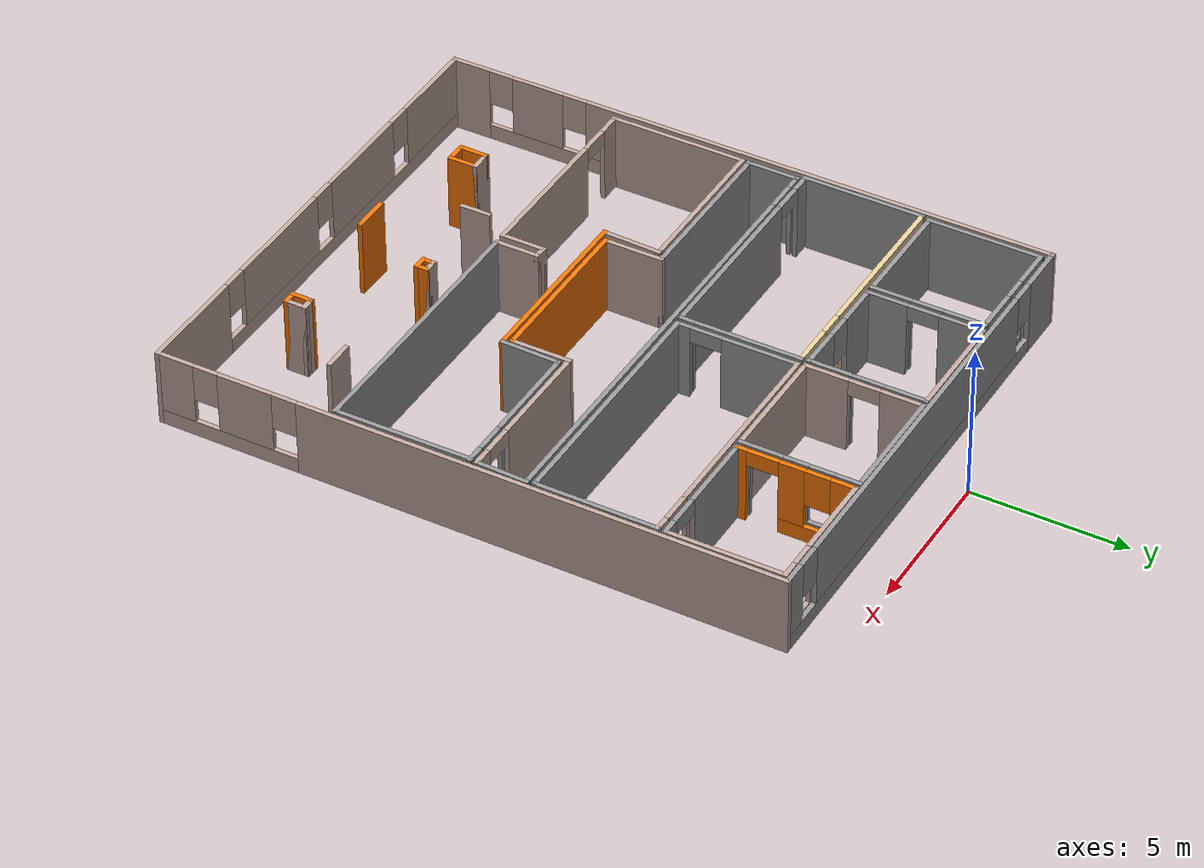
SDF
<?xml version='1.0'?>
<sdf version='1.6'>
  <model name='Testhaus1'>
    <pose frame=''>0.163791 -11.4063 0 0 -0 0</pose>
    <link name='Wall_10'>
      <collision name='Wall_10_Collision'>
        <geometry>
          <box>
            <size>3.78012 0.15 2.5</size>
          </box>
        </geometry>
        <pose frame=''>0 0 1.25 0 -0 0</pose>
      </collision>
      <visual name='Wall_10_Visual'>
        <pose frame=''>0 0 1.25 0 -0 0</pose>
        <geometry>
          <box>
            <size>3.78012 0.15 2.5</size>
          </box>
        </geometry>
        <material>
          <script>
            <uri>file://media/materials/scripts/gazebo.material</uri>
            <name>Gazebo/Grey</name>
          </script>
          <ambient>1 1 1 1</ambient>
        </material>
        <meta>
          <layer>0</layer>
        </meta>
      </visual>
      <pose frame=''>-6.11 6.2 0 0 -0 0</pose>
    </link>
    <link name='Wall_11'>
      <pose frame=''>-4.3 7.99 0 0 -0 1.57357</pose>
      <visual name='Wall_11_Visual_0'>
        <pose frame=''>-1.19399 0 1.25 0 -0 0</pose>
        <geometry>
          <box>
            <size>1.36203 0.15 2.5</size>
          </box>
        </geometry>
        <material>
          <script>
            <uri>file://media/materials/scripts/gazebo.material</uri>
            <name>Gazebo/Grey</name>
          </script>
          <ambient>1 1 1 1</ambient>
        </material>
        <meta>
          <layer>0</layer>
        </meta>
      </visual>
      <collision name='Wall_11_Collision_0'>
        <geometry>
          <box>
            <size>1.36203 0.15 2.5</size>
          </box>
        </geometry>
        <pose frame=''>-1.19399 0 1.25 0 -0 0</pose>
      </collision>
      <visual name='Wall_11_Visual_1'>
        <pose frame=''>1.18101 0 1.25 0 -0 0</pose>
        <geometry>
          <box>
            <size>1.38799 0.15 2.5</size>
          </box>
        </geometry>
        <material>
          <script>
            <uri>file://media/materials/scripts/gazebo.material</uri>
            <name>Gazebo/Grey</name>
          </script>
          <ambient>1 1 1 1</ambient>
        </material>
        <meta>
          <layer>0</layer>
        </meta>
      </visual>
      <collision name='Wall_11_Collision_1'>
        <geometry>
          <box>
            <size>1.38799 0.15 2.5</size>
          </box>
        </geometry>
        <pose frame=''>1.18101 0 1.25 0 -0 0</pose>
      </collision>
      <visual name='Wall_11_Visual_2'>
        <pose frame=''>-0.012979 0 2.25 0 -0 0</pose>
        <geometry>
          <box>
            <size>1 0.15 0.5</size>
          </box>
        </geometry>
        <material>
          <script>
            <uri>file://media/materials/scripts/gazebo.material</uri>
            <name>Gazebo/Grey</name>
          </script>
          <ambient>1 1 1 1</ambient>
        </material>
        <meta>
          <layer>0</layer>
        </meta>
      </visual>
      <collision name='Wall_11_Collision_2'>
        <geometry>
          <box>
            <size>1 0.15 0.5</size>
          </box>
        </geometry>
        <pose frame=''>-0.012979 0 2.25 0 -0 0</pose>
      </collision>
    </link>
    <link name='Wall_14'>
      <pose frame=''>-4.04051 8.02376 0 0 -0 -1.5708</pose>
      <visual name='Wall_14_Visual_0'>
        <pose frame=''>-1.18411 0 1.25 0 -0 0</pose>
        <geometry>
          <box>
            <size>1.46177 0.15 2.5</size>
          </box>
        </geometry>
        <material>
          <script>
            <uri>file://media/materials/scripts/gazebo.material</uri>
            <name>Gazebo/Grey</name>
          </script>
          <ambient>1 1 1 1</ambient>
        </material>
        <meta>
          <layer>0</layer>
        </meta>
      </visual>
      <collision name='Wall_14_Collision_0'>
        <geometry>
          <box>
            <size>1.46177 0.15 2.5</size>
          </box>
        </geometry>
        <pose frame=''>-1.18411 0 1.25 0 -0 0</pose>
      </collision>
      <visual name='Wall_14_Visual_1'>
        <pose frame=''>1.23089 0 1.25 0 -0 0</pose>
        <geometry>
          <box>
            <size>1.36823 0.15 2.5</size>
          </box>
        </geometry>
        <material>
          <script>
            <uri>file://media/materials/scripts/gazebo.material</uri>
            <name>Gazebo/Grey</name>
          </script>
          <ambient>1 1 1 1</ambient>
        </material>
        <meta>
          <layer>0</layer>
        </meta>
      </visual>
      <collision name='Wall_14_Collision_1'>
        <geometry>
          <box>
            <size>1.36823 0.15 2.5</size>
          </box>
        </geometry>
        <pose frame=''>1.23089 0 1.25 0 -0 0</pose>
      </collision>
      <visual name='Wall_14_Visual_2'>
        <pose frame=''>0.046771 0 2.25 0 -0 0</pose>
        <geometry>
          <box>
            <size>1 0.15 0.5</size>
          </box>
        </geometry>
        <material>
          <script>
            <uri>file://media/materials/scripts/gazebo.material</uri>
            <name>Gazebo/Grey</name>
          </script>
          <ambient>1 1 1 1</ambient>
        </material>
        <meta>
          <layer>0</layer>
        </meta>
      </visual>
      <collision name='Wall_14_Collision_2'>
        <geometry>
          <box>
            <size>1 0.15 0.5</size>
          </box>
        </geometry>
        <pose frame=''>0.046771 0 2.25 0 -0 0</pose>
      </collision>
    </link>
    <link name='Wall_15'>
      <pose frame=''>-2.24051 6.18377 0 0 -0 0</pose>
      <visual name='Wall_15_Visual_0'>
        <pose frame=''>-1.12575 0 1.25 0 -0 0</pose>
        <geometry>
          <box>
            <size>1.49849 0.15 2.5</size>
          </box>
        </geometry>
        <material>
          <script>
            <uri>file://media/materials/scripts/gazebo.material</uri>
            <name>Gazebo/Grey</name>
          </script>
          <ambient>1 1 1 1</ambient>
        </material>
        <meta>
          <layer>0</layer>
        </meta>
      </visual>
      <collision name='Wall_15_Collision_0'>
        <geometry>
          <box>
            <size>1.49849 0.15 2.5</size>
          </box>
        </geometry>
        <pose frame=''>-1.12575 0 1.25 0 -0 0</pose>
      </collision>
      <visual name='Wall_15_Visual_1'>
        <pose frame=''>0.749247 0 0.25 0 -0 0</pose>
        <geometry>
          <box>
            <size>2.2515 0.15 0.5</size>
          </box>
        </geometry>
        <material>
          <script>
            <uri>file://media/materials/scripts/gazebo.material</uri>
            <name>Gazebo/Grey</name>
          </script>
          <ambient>1 1 1 1</ambient>
        </material>
        <meta>
          <layer>0</layer>
        </meta>
      </visual>
      <collision name='Wall_15_Collision_1'>
        <geometry>
          <box>
            <size>2.2515 0.15 0.5</size>
          </box>
        </geometry>
        <pose frame=''>0.749247 0 0.25 0 -0 0</pose>
      </collision>
      <visual name='Wall_15_Visual_2'>
        <pose frame=''>1.14925 0 1.5 0 -0 0</pose>
        <geometry>
          <box>
            <size>1.45151 0.15 2</size>
          </box>
        </geometry>
        <material>
          <script>
            <uri>file://media/materials/scripts/gazebo.material</uri>
            <name>Gazebo/Grey</name>
          </script>
          <ambient>1 1 1 1</ambient>
        </material>
        <meta>
          <layer>0</layer>
        </meta>
      </visual>
      <collision name='Wall_15_Collision_2'>
        <geometry>
          <box>
            <size>1.45151 0.15 2</size>
          </box>
        </geometry>
        <pose frame=''>1.14925 0 1.5 0 -0 0</pose>
      </collision>
      <visual name='Wall_15_Visual_3'>
        <pose frame=''>0.023495 0 1.9 0 -0 0</pose>
        <geometry>
          <box>
            <size>0.8 0.15 1.2</size>
          </box>
        </geometry>
        <material>
          <script>
            <uri>file://media/materials/scripts/gazebo.material</uri>
            <name>Gazebo/Grey</name>
          </script>
          <ambient>1 1 1 1</ambient>
        </material>
        <meta>
          <layer>0</layer>
        </meta>
      </visual>
      <collision name='Wall_15_Collision_3'>
        <geometry>
          <box>
            <size>0.8 0.15 1.2</size>
          </box>
        </geometry>
        <pose frame=''>0.023495 0 1.9 0 -0 0</pose>
      </collision>
    </link>
    <link name='Wall_16'>
      <pose frame=''>-0.440512 8.02376 0 0 -0 1.5708</pose>
      <visual name='Wall_16_Visual_0'>
        <pose frame=''>-1.19129 0 1.25 0 -0 0</pose>
        <geometry>
          <box>
            <size>1.44742 0.15 2.5</size>
          </box>
        </geometry>
        <material>
          <script>
            <uri>file://media/materials/scripts/gazebo.material</uri>
            <name>Gazebo/Grey</name>
          </script>
          <ambient>1 1 1 1</ambient>
        </material>
        <meta>
          <layer>0</layer>
        </meta>
      </visual>
      <collision name='Wall_16_Collision_0'>
        <geometry>
          <box>
            <size>1.44742 0.15 2.5</size>
          </box>
        </geometry>
        <pose frame=''>-1.19129 0 1.25 0 -0 0</pose>
      </collision>
      <visual name='Wall_16_Visual_1'>
        <pose frame=''>1.22371 0 1.25 0 -0 0</pose>
        <geometry>
          <box>
            <size>1.38258 0.15 2.5</size>
          </box>
        </geometry>
        <material>
          <script>
            <uri>file://media/materials/scripts/gazebo.material</uri>
            <name>Gazebo/Grey</name>
          </script>
          <ambient>1 1 1 1</ambient>
        </material>
        <meta>
          <layer>0</layer>
        </meta>
      </visual>
      <collision name='Wall_16_Collision_1'>
        <geometry>
          <box>
            <size>1.38258 0.15 2.5</size>
          </box>
        </geometry>
        <pose frame=''>1.22371 0 1.25 0 -0 0</pose>
      </collision>
      <visual name='Wall_16_Visual_2'>
        <pose frame=''>0.032421 0 2.25 0 -0 0</pose>
        <geometry>
          <box>
            <size>1 0.15 0.5</size>
          </box>
        </geometry>
        <material>
          <script>
            <uri>file://media/materials/scripts/gazebo.material</uri>
            <name>Gazebo/Grey</name>
          </script>
          <ambient>1 1 1 1</ambient>
        </material>
        <meta>
          <layer>0</layer>
        </meta>
      </visual>
      <collision name='Wall_16_Collision_2'>
        <geometry>
          <box>
            <size>1 0.15 0.5</size>
          </box>
        </geometry>
        <pose frame=''>0.032421 0 2.25 0 -0 0</pose>
      </collision>
    </link>
    <link name='Wall_17'>
      <collision name='Wall_17_Collision'>
        <geometry>
          <box>
            <size>3.75 0.15 2.5</size>
          </box>
        </geometry>
        <pose frame=''>0 0 1.25 0 -0 0</pose>
      </collision>
      <visual name='Wall_17_Visual'>
        <pose frame=''>0 0 1.25 0 -0 0</pose>
        <geometry>
          <box>
            <size>3.75 0.15 2.5</size>
          </box>
        </geometry>
        <material>
          <script>
            <uri>file://media/materials/scripts/gazebo.material</uri>
            <name>Gazebo/Grey</name>
          </script>
          <ambient>0.760784 0.662745 0.627451 1</ambient>
        </material>
        <meta>
          <layer>0</layer>
        </meta>
      </visual>
      <pose frame=''>-2.24051 9.87377 0 0 -0 3.14159</pose>
    </link>
    <link name='Wall_19'>
      <pose frame=''>-0.210083 8.02674 0 0 -0 1.5708</pose>
      <visual name='Wall_19_Visual_0'>
        <pose frame=''>-1.19778 0 1.25 0 -0 0</pose>
        <geometry>
          <box>
            <size>1.45445 0.15 2.5</size>
          </box>
        </geometry>
        <material>
          <script>
            <uri>file://media/materials/scripts/gazebo.material</uri>
            <name>Gazebo/Grey</name>
          </script>
          <ambient>0.760784 0.662745 0.627451 1</ambient>
        </material>
        <meta>
          <layer>0</layer>
        </meta>
      </visual>
      <collision name='Wall_19_Collision_0'>
        <geometry>
          <box>
            <size>1.45445 0.15 2.5</size>
          </box>
        </geometry>
        <pose frame=''>-1.19778 0 1.25 0 -0 0</pose>
      </collision>
      <visual name='Wall_19_Visual_1'>
        <pose frame=''>1.22723 0 1.25 0 -0 0</pose>
        <geometry>
          <box>
            <size>1.39555 0.15 2.5</size>
          </box>
        </geometry>
        <material>
          <script>
            <uri>file://media/materials/scripts/gazebo.material</uri>
            <name>Gazebo/Grey</name>
          </script>
          <ambient>0.760784 0.662745 0.627451 1</ambient>
        </material>
        <meta>
          <layer>0</layer>
        </meta>
      </visual>
      <collision name='Wall_19_Collision_1'>
        <geometry>
          <box>
            <size>1.39555 0.15 2.5</size>
          </box>
        </geometry>
        <pose frame=''>1.22723 0 1.25 0 -0 0</pose>
      </collision>
      <visual name='Wall_19_Visual_2'>
        <pose frame=''>0.02945 0 2.25 0 -0 0</pose>
        <geometry>
          <box>
            <size>1 0.15 0.5</size>
          </box>
        </geometry>
        <material>
          <script>
            <uri>file://media/materials/scripts/gazebo.material</uri>
            <name>Gazebo/Grey</name>
          </script>
          <ambient>0.760784 0.662745 0.627451 1</ambient>
        </material>
        <meta>
          <layer>0</layer>
        </meta>
      </visual>
      <collision name='Wall_19_Collision_2'>
        <geometry>
          <box>
            <size>1 0.15 0.5</size>
          </box>
        </geometry>
        <pose frame=''>0.02945 0 2.25 0 -0 0</pose>
      </collision>
    </link>
    <link name='Wall_20'>
      <collision name='Wall_20_Collision'>
        <geometry>
          <box>
            <size>4 0.15 2.5</size>
          </box>
        </geometry>
        <pose frame=''>0 0 1.25 0 -0 0</pose>
      </collision>
      <visual name='Wall_20_Visual'>
        <pose frame=''>0 0 1.25 0 -0 0</pose>
        <geometry>
          <box>
            <size>4 0.15 2.5</size>
          </box>
        </geometry>
        <material>
          <script>
            <uri>file://media/materials/scripts/gazebo.material</uri>
            <name>Gazebo/Grey</name>
          </script>
          <ambient>1 1 1 1</ambient>
        </material>
        <meta>
          <layer>0</layer>
        </meta>
      </visual>
      <pose frame=''>1.71492 9.88674 0 0 -0 0</pose>
    </link>
    <link name='Wall_21'>
      <pose frame=''>3.63992 8.02674 0 0 -0 -1.5708</pose>
      <visual name='Wall_21_Visual_0'>
        <pose frame=''>-1.51075 0 1.25 0 -0 0</pose>
        <geometry>
          <box>
            <size>0.828493 0.15 2.5</size>
          </box>
        </geometry>
        <material>
          <script>
            <uri>file://media/materials/scripts/gazebo.material</uri>
            <name>Gazebo/Grey</name>
          </script>
          <ambient>1 1 1 1</ambient>
        </material>
        <meta>
          <layer>0</layer>
        </meta>
      </visual>
      <collision name='Wall_21_Collision_0'>
        <geometry>
          <box>
            <size>0.828493 0.15 2.5</size>
          </box>
        </geometry>
        <pose frame=''>-1.51075 0 1.25 0 -0 0</pose>
      </collision>
      <visual name='Wall_21_Visual_1'>
        <pose frame=''>1.71575 0 1.25 0 -0 0</pose>
        <geometry>
          <box>
            <size>0.418499 0.15 2.5</size>
          </box>
        </geometry>
        <material>
          <script>
            <uri>file://media/materials/scripts/gazebo.material</uri>
            <name>Gazebo/Grey</name>
          </script>
          <ambient>1 1 1 1</ambient>
        </material>
        <meta>
          <layer>0</layer>
        </meta>
      </visual>
      <collision name='Wall_21_Collision_1'>
        <geometry>
          <box>
            <size>0.418499 0.15 2.5</size>
          </box>
        </geometry>
        <pose frame=''>1.71575 0 1.25 0 -0 0</pose>
      </collision>
      <visual name='Wall_21_Visual_2'>
        <pose frame=''>-0.295003 0 0.25 0 -0 0</pose>
        <geometry>
          <box>
            <size>1.60301 0.15 0.5</size>
          </box>
        </geometry>
        <material>
          <script>
            <uri>file://media/materials/scripts/gazebo.material</uri>
            <name>Gazebo/Grey</name>
          </script>
          <ambient>1 1 1 1</ambient>
        </material>
        <meta>
          <layer>0</layer>
        </meta>
      </visual>
      <collision name='Wall_21_Collision_2'>
        <geometry>
          <box>
            <size>1.60301 0.15 0.5</size>
          </box>
        </geometry>
        <pose frame=''>-0.295003 0 0.25 0 -0 0</pose>
      </collision>
      <visual name='Wall_21_Visual_3'>
        <pose frame=''>0.104997 0 1.5 0 -0 0</pose>
        <geometry>
          <box>
            <size>0.803009 0.15 2</size>
          </box>
        </geometry>
        <material>
          <script>
            <uri>file://media/materials/scripts/gazebo.material</uri>
            <name>Gazebo/Grey</name>
          </script>
          <ambient>1 1 1 1</ambient>
        </material>
        <meta>
          <layer>0</layer>
        </meta>
      </visual>
      <collision name='Wall_21_Collision_3'>
        <geometry>
          <box>
            <size>0.803009 0.15 2</size>
          </box>
        </geometry>
        <pose frame=''>0.104997 0 1.5 0 -0 0</pose>
      </collision>
      <visual name='Wall_21_Visual_4'>
        <pose frame=''>-0.696507 0 1.9 0 -0 0</pose>
        <geometry>
          <box>
            <size>0.8 0.15 1.2</size>
          </box>
        </geometry>
        <material>
          <script>
            <uri>file://media/materials/scripts/gazebo.material</uri>
            <name>Gazebo/Grey</name>
          </script>
          <ambient>1 1 1 1</ambient>
        </material>
        <meta>
          <layer>0</layer>
        </meta>
      </visual>
      <collision name='Wall_21_Collision_4'>
        <geometry>
          <box>
            <size>0.8 0.15 1.2</size>
          </box>
        </geometry>
        <pose frame=''>-0.696507 0 1.9 0 -0 0</pose>
      </collision>
      <visual name='Wall_21_Visual_5'>
        <pose frame=''>1.0065 0 2.25 0 -0 0</pose>
        <geometry>
          <box>
            <size>1 0.15 0.5</size>
          </box>
        </geometry>
        <material>
          <script>
            <uri>file://media/materials/scripts/gazebo.material</uri>
            <name>Gazebo/Grey</name>
          </script>
          <ambient>1 1 1 1</ambient>
        </material>
        <meta>
          <layer>0</layer>
        </meta>
      </visual>
      <collision name='Wall_21_Collision_5'>
        <geometry>
          <box>
            <size>1 0.15 0.5</size>
          </box>
        </geometry>
        <pose frame=''>1.0065 0 2.25 0 -0 0</pose>
      </collision>
    </link>
    <link name='Wall_22'>
      <collision name='Wall_22_Collision'>
        <geometry>
          <box>
            <size>4 0.15 2.5</size>
          </box>
        </geometry>
        <pose frame=''>0 0 1.25 0 -0 0</pose>
      </collision>
      <visual name='Wall_22_Visual'>
        <pose frame=''>0 0 1.25 0 -0 0</pose>
        <geometry>
          <box>
            <size>4 0.15 2.5</size>
          </box>
        </geometry>
        <material>
          <script>
            <uri>file://media/materials/scripts/gazebo.material</uri>
            <name>Gazebo/Grey</name>
          </script>
          <ambient>0.760784 0.662745 0.627451 1</ambient>
        </material>
        <meta>
          <layer>0</layer>
        </meta>
      </visual>
      <pose frame=''>1.71492 6.17674 0 0 -0 3.14159</pose>
    </link>
    <link name='Wall_25'>
      <pose frame=''>3.87412 8.04618 0 0 -0 -1.56808</pose>
      <visual name='Wall_25_Visual_0'>
        <pose frame=''>-1.49608 0 1.25 0 -0 0</pose>
        <geometry>
          <box>
            <size>0.837861 0.15 2.5</size>
          </box>
        </geometry>
        <material>
          <script>
            <uri>file://media/materials/scripts/gazebo.material</uri>
            <name>Gazebo/Grey</name>
          </script>
          <ambient>0.996078 0.47451 0.0196078 1</ambient>
        </material>
        <meta>
          <layer>0</layer>
        </meta>
      </visual>
      <collision name='Wall_25_Collision_0'>
        <geometry>
          <box>
            <size>0.837861 0.15 2.5</size>
          </box>
        </geometry>
        <pose frame=''>-1.49608 0 1.25 0 -0 0</pose>
      </collision>
      <visual name='Wall_25_Visual_1'>
        <pose frame=''>1.72051 0 1.25 0 -0 0</pose>
        <geometry>
          <box>
            <size>0.388999 0.15 2.5</size>
          </box>
        </geometry>
        <material>
          <script>
            <uri>file://media/materials/scripts/gazebo.material</uri>
            <name>Gazebo/Grey</name>
          </script>
          <ambient>0.996078 0.47451 0.0196078 1</ambient>
        </material>
        <meta>
          <layer>0</layer>
        </meta>
      </visual>
      <collision name='Wall_25_Collision_1'>
        <geometry>
          <box>
            <size>0.388999 0.15 2.5</size>
          </box>
        </geometry>
        <pose frame=''>1.72051 0 1.25 0 -0 0</pose>
      </collision>
      <visual name='Wall_25_Visual_2'>
        <pose frame=''>-0.275569 0 0.25 0 -0 0</pose>
        <geometry>
          <box>
            <size>1.60315 0.15 0.5</size>
          </box>
        </geometry>
        <material>
          <script>
            <uri>file://media/materials/scripts/gazebo.material</uri>
            <name>Gazebo/Grey</name>
          </script>
          <ambient>0.996078 0.47451 0.0196078 1</ambient>
        </material>
        <meta>
          <layer>0</layer>
        </meta>
      </visual>
      <collision name='Wall_25_Collision_2'>
        <geometry>
          <box>
            <size>1.60315 0.15 0.5</size>
          </box>
        </geometry>
        <pose frame=''>-0.275569 0 0.25 0 -0 0</pose>
      </collision>
      <visual name='Wall_25_Visual_3'>
        <pose frame=''>0.124431 0 1.5 0 -0 0</pose>
        <geometry>
          <box>
            <size>0.803154 0.15 2</size>
          </box>
        </geometry>
        <material>
          <script>
            <uri>file://media/materials/scripts/gazebo.material</uri>
            <name>Gazebo/Grey</name>
          </script>
          <ambient>0.996078 0.47451 0.0196078 1</ambient>
        </material>
        <meta>
          <layer>0</layer>
        </meta>
      </visual>
      <collision name='Wall_25_Collision_3'>
        <geometry>
          <box>
            <size>0.803154 0.15 2</size>
          </box>
        </geometry>
        <pose frame=''>0.124431 0 1.5 0 -0 0</pose>
      </collision>
      <visual name='Wall_25_Visual_4'>
        <pose frame=''>-0.677146 0 1.9 0 -0 0</pose>
        <geometry>
          <box>
            <size>0.8 0.15 1.2</size>
          </box>
        </geometry>
        <material>
          <script>
            <uri>file://media/materials/scripts/gazebo.material</uri>
            <name>Gazebo/Grey</name>
          </script>
          <ambient>0.996078 0.47451 0.0196078 1</ambient>
        </material>
        <meta>
          <layer>0</layer>
        </meta>
      </visual>
      <collision name='Wall_25_Collision_4'>
        <geometry>
          <box>
            <size>0.8 0.15 1.2</size>
          </box>
        </geometry>
        <pose frame=''>-0.677146 0 1.9 0 -0 0</pose>
      </collision>
      <visual name='Wall_25_Visual_5'>
        <pose frame=''>1.02601 0 2.25 0 -0 0</pose>
        <geometry>
          <box>
            <size>1 0.15 0.5</size>
          </box>
        </geometry>
        <material>
          <script>
            <uri>file://media/materials/scripts/gazebo.material</uri>
            <name>Gazebo/Grey</name>
          </script>
          <ambient>0.996078 0.47451 0.0196078 1</ambient>
        </material>
        <meta>
          <layer>0</layer>
        </meta>
      </visual>
      <collision name='Wall_25_Collision_5'>
        <geometry>
          <box>
            <size>1 0.15 0.5</size>
          </box>
        </geometry>
        <pose frame=''>1.02601 0 2.25 0 -0 0</pose>
      </collision>
    </link>
    <link name='Wall_26'>
      <pose frame=''>5.92912 6.20618 0 0 -0 0</pose>
      <visual name='Wall_26_Visual_0'>
        <pose frame=''>-0.789086 0 1.25 0 -0 0</pose>
        <geometry>
          <box>
            <size>2.67183 0.15 2.5</size>
          </box>
        </geometry>
        <material>
          <script>
            <uri>file://media/materials/scripts/gazebo.material</uri>
            <name>Gazebo/Grey</name>
          </script>
          <ambient>1 1 1 1</ambient>
        </material>
        <meta>
          <layer>0</layer>
        </meta>
      </visual>
      <collision name='Wall_26_Collision_0'>
        <geometry>
          <box>
            <size>2.67183 0.15 2.5</size>
          </box>
        </geometry>
        <pose frame=''>-0.789086 0 1.25 0 -0 0</pose>
      </collision>
      <visual name='Wall_26_Visual_1'>
        <pose frame=''>1.83591 0 1.25 0 -0 0</pose>
        <geometry>
          <box>
            <size>0.578171 0.15 2.5</size>
          </box>
        </geometry>
        <material>
          <script>
            <uri>file://media/materials/scripts/gazebo.material</uri>
            <name>Gazebo/Grey</name>
          </script>
          <ambient>1 1 1 1</ambient>
        </material>
        <meta>
          <layer>0</layer>
        </meta>
      </visual>
      <collision name='Wall_26_Collision_1'>
        <geometry>
          <box>
            <size>0.578171 0.15 2.5</size>
          </box>
        </geometry>
        <pose frame=''>1.83591 0 1.25 0 -0 0</pose>
      </collision>
      <visual name='Wall_26_Visual_2'>
        <pose frame=''>1.04683 0 2.25 0 -0 0</pose>
        <geometry>
          <box>
            <size>1 0.15 0.5</size>
          </box>
        </geometry>
        <material>
          <script>
            <uri>file://media/materials/scripts/gazebo.material</uri>
            <name>Gazebo/Grey</name>
          </script>
          <ambient>1 1 1 1</ambient>
        </material>
        <meta>
          <layer>0</layer>
        </meta>
      </visual>
      <collision name='Wall_26_Collision_2'>
        <geometry>
          <box>
            <size>1 0.15 0.5</size>
          </box>
        </geometry>
        <pose frame=''>1.04683 0 2.25 0 -0 0</pose>
      </collision>
    </link>
    <link name='Wall_27'>
      <collision name='Wall_27_Collision'>
        <geometry>
          <box>
            <size>3.83001 0.15 2.5</size>
          </box>
        </geometry>
        <pose frame=''>0 0 1.25 0 -0 0</pose>
      </collision>
      <visual name='Wall_27_Visual'>
        <pose frame=''>0 0 1.25 0 -0 0</pose>
        <geometry>
          <box>
            <size>3.83001 0.15 2.5</size>
          </box>
        </geometry>
        <material>
          <script>
            <uri>file://media/materials/scripts/gazebo.material</uri>
            <name>Gazebo/Grey</name>
          </script>
          <ambient>0.760784 0.662745 0.627451 1</ambient>
        </material>
        <meta>
          <layer>0</layer>
        </meta>
      </visual>
      <pose frame=''>7.97412 8.04618 0 0 -0 1.57351</pose>
    </link>
    <link name='Wall_28'>
      <pose frame=''>5.91912 9.87618 0 0 -0 3.14159</pose>
      <visual name='Wall_28_Visual_0'>
        <pose frame=''>-1.81839 0 1.25 0 -0 0</pose>
        <geometry>
          <box>
            <size>0.613212 0.15 2.5</size>
          </box>
        </geometry>
        <material>
          <script>
            <uri>file://media/materials/scripts/gazebo.material</uri>
            <name>Gazebo/Grey</name>
          </script>
          <ambient>0.760784 0.662745 0.627451 1</ambient>
        </material>
        <meta>
          <layer>0</layer>
        </meta>
      </visual>
      <collision name='Wall_28_Collision_0'>
        <geometry>
          <box>
            <size>0.613212 0.15 2.5</size>
          </box>
        </geometry>
        <pose frame=''>-1.81839 0 1.25 0 -0 0</pose>
      </collision>
      <visual name='Wall_28_Visual_1'>
        <pose frame=''>0.306606 0 0.25 0 -0 0</pose>
        <geometry>
          <box>
            <size>3.63679 0.15 0.5</size>
          </box>
        </geometry>
        <material>
          <script>
            <uri>file://media/materials/scripts/gazebo.material</uri>
            <name>Gazebo/Grey</name>
          </script>
          <ambient>0.760784 0.662745 0.627451 1</ambient>
        </material>
        <meta>
          <layer>0</layer>
        </meta>
      </visual>
      <collision name='Wall_28_Collision_1'>
        <geometry>
          <box>
            <size>3.63679 0.15 0.5</size>
          </box>
        </geometry>
        <pose frame=''>0.306606 0 0.25 0 -0 0</pose>
      </collision>
      <visual name='Wall_28_Visual_2'>
        <pose frame=''>0.706606 0 1.5 0 -0 0</pose>
        <geometry>
          <box>
            <size>2.83679 0.15 2</size>
          </box>
        </geometry>
        <material>
          <script>
            <uri>file://media/materials/scripts/gazebo.material</uri>
            <name>Gazebo/Grey</name>
          </script>
          <ambient>0.760784 0.662745 0.627451 1</ambient>
        </material>
        <meta>
          <layer>0</layer>
        </meta>
      </visual>
      <collision name='Wall_28_Collision_2'>
        <geometry>
          <box>
            <size>2.83679 0.15 2</size>
          </box>
        </geometry>
        <pose frame=''>0.706606 0 1.5 0 -0 0</pose>
      </collision>
      <visual name='Wall_28_Visual_3'>
        <pose frame=''>-1.11179 0 1.9 0 -0 0</pose>
        <geometry>
          <box>
            <size>0.8 0.15 1.2</size>
          </box>
        </geometry>
        <material>
          <script>
            <uri>file://media/materials/scripts/gazebo.material</uri>
            <name>Gazebo/Grey</name>
          </script>
          <ambient>0.760784 0.662745 0.627451 1</ambient>
        </material>
        <meta>
          <layer>0</layer>
        </meta>
      </visual>
      <collision name='Wall_28_Collision_3'>
        <geometry>
          <box>
            <size>0.8 0.15 1.2</size>
          </box>
        </geometry>
        <pose frame=''>-1.11179 0 1.9 0 -0 0</pose>
      </collision>
    </link>
    <link name='Wall_30'>
      <collision name='Wall_30_Collision'>
        <geometry>
          <box>
            <size>3.75 0.15 2.5</size>
          </box>
        </geometry>
        <pose frame=''>0 0 1.25 0 -0 0</pose>
      </collision>
      <visual name='Wall_30_Visual'>
        <pose frame=''>0 0 1.25 0 -0 0</pose>
        <geometry>
          <box>
            <size>3.75 0.15 2.5</size>
          </box>
        </geometry>
        <material>
          <script>
            <uri>file://media/materials/scripts/gazebo.material</uri>
            <name>Gazebo/Grey</name>
          </script>
          <ambient>1 1 1 1</ambient>
        </material>
        <meta>
          <layer>0</layer>
        </meta>
      </visual>
      <pose frame=''>-7.925 8 0 0 -0 1.5708</pose>
    </link>
    <link name='Wall_33'>
      <pose frame=''>-6.115 9.795 0 0 -0 -0.002762</pose>
      <visual name='Wall_33_Visual_0'>
        <pose frame=''>-1.1885 0 1.25 0 -0 0</pose>
        <geometry>
          <box>
            <size>1.39302 0.15 2.5</size>
          </box>
        </geometry>
        <material>
          <script>
            <uri>file://media/materials/scripts/gazebo.material</uri>
            <name>Gazebo/Grey</name>
          </script>
          <ambient>1 1 1 1</ambient>
        </material>
        <meta>
          <layer>0</layer>
        </meta>
      </visual>
      <collision name='Wall_33_Collision_0'>
        <geometry>
          <box>
            <size>1.39302 0.15 2.5</size>
          </box>
        </geometry>
        <pose frame=''>-1.1885 0 1.25 0 -0 0</pose>
      </collision>
      <visual name='Wall_33_Visual_1'>
        <pose frame=''>0.696509 0 0.25 0 -0 0</pose>
        <geometry>
          <box>
            <size>2.37699 0.15 0.5</size>
          </box>
        </geometry>
        <material>
          <script>
            <uri>file://media/materials/scripts/gazebo.material</uri>
            <name>Gazebo/Grey</name>
          </script>
          <ambient>1 1 1 1</ambient>
        </material>
        <meta>
          <layer>0</layer>
        </meta>
      </visual>
      <collision name='Wall_33_Collision_1'>
        <geometry>
          <box>
            <size>2.37699 0.15 0.5</size>
          </box>
        </geometry>
        <pose frame=''>0.696509 0 0.25 0 -0 0</pose>
      </collision>
      <visual name='Wall_33_Visual_2'>
        <pose frame=''>1.09651 0 1.5 0 -0 0</pose>
        <geometry>
          <box>
            <size>1.57699 0.15 2</size>
          </box>
        </geometry>
        <material>
          <script>
            <uri>file://media/materials/scripts/gazebo.material</uri>
            <name>Gazebo/Grey</name>
          </script>
          <ambient>1 1 1 1</ambient>
        </material>
        <meta>
          <layer>0</layer>
        </meta>
      </visual>
      <collision name='Wall_33_Collision_2'>
        <geometry>
          <box>
            <size>1.57699 0.15 2</size>
          </box>
        </geometry>
        <pose frame=''>1.09651 0 1.5 0 -0 0</pose>
      </collision>
      <visual name='Wall_33_Visual_3'>
        <pose frame=''>-0.091988 0 1.9 0 -0 0</pose>
        <geometry>
          <box>
            <size>0.8 0.15 1.2</size>
          </box>
        </geometry>
        <material>
          <script>
            <uri>file://media/materials/scripts/gazebo.material</uri>
            <name>Gazebo/Grey</name>
          </script>
          <ambient>1 1 1 1</ambient>
        </material>
        <meta>
          <layer>0</layer>
        </meta>
      </visual>
      <collision name='Wall_33_Collision_3'>
        <geometry>
          <box>
            <size>0.8 0.15 1.2</size>
          </box>
        </geometry>
        <pose frame=''>-0.091988 0 1.9 0 -0 0</pose>
      </collision>
    </link>
    <link name='Wall_35'>
      <pose frame=''>3.91023 5.9629 0 0 -0 3.14159</pose>
      <visual name='Wall_35_Visual_0'>
        <pose frame=''>-3.84536 0 1.25 0 -0 0</pose>
        <geometry>
          <box>
            <size>0.559283 0.15 2.5</size>
          </box>
        </geometry>
        <material>
          <script>
            <uri>file://media/materials/scripts/gazebo.material</uri>
            <name>Gazebo/Grey</name>
          </script>
          <ambient>0.760784 0.662745 0.627451 1</ambient>
        </material>
        <meta>
          <layer>0</layer>
        </meta>
      </visual>
      <collision name='Wall_35_Collision_0'>
        <geometry>
          <box>
            <size>0.559283 0.15 2.5</size>
          </box>
        </geometry>
        <pose frame=''>-3.84536 0 1.25 0 -0 0</pose>
      </collision>
      <visual name='Wall_35_Visual_1'>
        <pose frame=''>0.779642 0 1.25 0 -0 0</pose>
        <geometry>
          <box>
            <size>6.69072 0.15 2.5</size>
          </box>
        </geometry>
        <material>
          <script>
            <uri>file://media/materials/scripts/gazebo.material</uri>
            <name>Gazebo/Grey</name>
          </script>
          <ambient>0.760784 0.662745 0.627451 1</ambient>
        </material>
        <meta>
          <layer>0</layer>
        </meta>
      </visual>
      <collision name='Wall_35_Collision_1'>
        <geometry>
          <box>
            <size>6.69072 0.15 2.5</size>
          </box>
        </geometry>
        <pose frame=''>0.779642 0 1.25 0 -0 0</pose>
      </collision>
      <visual name='Wall_35_Visual_2'>
        <pose frame=''>-3.06572 0 2.25 0 -0 0</pose>
        <geometry>
          <box>
            <size>1 0.15 0.5</size>
          </box>
        </geometry>
        <material>
          <script>
            <uri>file://media/materials/scripts/gazebo.material</uri>
            <name>Gazebo/Grey</name>
          </script>
          <ambient>0.760784 0.662745 0.627451 1</ambient>
        </material>
        <meta>
          <layer>0</layer>
        </meta>
      </visual>
      <collision name='Wall_35_Collision_2'>
        <geometry>
          <box>
            <size>1 0.15 0.5</size>
          </box>
        </geometry>
        <pose frame=''>-3.06572 0 2.25 0 -0 0</pose>
      </collision>
    </link>
    <link name='Wall_36'>
      <pose frame=''>-0.13977 4.0379 0 0 -0 -1.5708</pose>
      <visual name='Wall_36_Visual_0'>
        <pose frame=''>-0.753952 0 1.25 0 -0 0</pose>
        <geometry>
          <box>
            <size>2.4921 0.15 2.5</size>
          </box>
        </geometry>
        <material>
          <script>
            <uri>file://media/materials/scripts/gazebo.material</uri>
            <name>Gazebo/Grey</name>
          </script>
          <ambient>1 1 1 1</ambient>
        </material>
        <meta>
          <layer>0</layer>
        </meta>
      </visual>
      <collision name='Wall_36_Collision_0'>
        <geometry>
          <box>
            <size>2.4921 0.15 2.5</size>
          </box>
        </geometry>
        <pose frame=''>-0.753952 0 1.25 0 -0 0</pose>
      </collision>
      <visual name='Wall_36_Visual_1'>
        <pose frame=''>1.74605 0 1.25 0 -0 0</pose>
        <geometry>
          <box>
            <size>0.507903 0.15 2.5</size>
          </box>
        </geometry>
        <material>
          <script>
            <uri>file://media/materials/scripts/gazebo.material</uri>
            <name>Gazebo/Grey</name>
          </script>
          <ambient>1 1 1 1</ambient>
        </material>
        <meta>
          <layer>0</layer>
        </meta>
      </visual>
      <collision name='Wall_36_Collision_1'>
        <geometry>
          <box>
            <size>0.507903 0.15 2.5</size>
          </box>
        </geometry>
        <pose frame=''>1.74605 0 1.25 0 -0 0</pose>
      </collision>
      <visual name='Wall_36_Visual_2'>
        <pose frame=''>0.992097 0 2.25 0 -0 0</pose>
        <geometry>
          <box>
            <size>1 0.15 0.5</size>
          </box>
        </geometry>
        <material>
          <script>
            <uri>file://media/materials/scripts/gazebo.material</uri>
            <name>Gazebo/Grey</name>
          </script>
          <ambient>1 1 1 1</ambient>
        </material>
        <meta>
          <layer>0</layer>
        </meta>
      </visual>
      <collision name='Wall_36_Collision_2'>
        <geometry>
          <box>
            <size>1 0.15 0.5</size>
          </box>
        </geometry>
        <pose frame=''>0.992097 0 2.25 0 -0 0</pose>
      </collision>
    </link>
    <link name='Wall_37'>
      <collision name='Wall_37_Collision'>
        <geometry>
          <box>
            <size>8.25 0.15 2.5</size>
          </box>
        </geometry>
        <pose frame=''>0 0 1.25 0 -0 0</pose>
      </collision>
      <visual name='Wall_37_Visual'>
        <pose frame=''>0 0 1.25 0 -0 0</pose>
        <geometry>
          <box>
            <size>8.25 0.15 2.5</size>
          </box>
        </geometry>
        <material>
          <script>
            <uri>file://media/materials/scripts/gazebo.material</uri>
            <name>Gazebo/Grey</name>
          </script>
          <ambient>1 1 1 1</ambient>
        </material>
        <meta>
          <layer>0</layer>
        </meta>
      </visual>
      <pose frame=''>3.91023 2.1129 0 0 -0 0</pose>
    </link>
    <link name='Wall_38'>
      <collision name='Wall_38_Collision'>
        <geometry>
          <box>
            <size>4 0.15 2.5</size>
          </box>
        </geometry>
        <pose frame=''>0 0 1.25 0 -0 0</pose>
      </collision>
      <visual name='Wall_38_Visual'>
        <pose frame=''>0 0 1.25 0 -0 0</pose>
        <geometry>
          <box>
            <size>4 0.15 2.5</size>
          </box>
        </geometry>
        <material>
          <script>
            <uri>file://media/materials/scripts/gazebo.material</uri>
            <name>Gazebo/Grey</name>
          </script>
          <ambient>1 1 1 1</ambient>
        </material>
        <meta>
          <layer>0</layer>
        </meta>
      </visual>
      <pose frame=''>7.96023 4.0379 0 0 -0 1.5708</pose>
    </link>
    <link name='Wall_4'>
      <pose frame=''>-0 10.05 0 0 -0 0</pose>
      <visual name='Wall_4_Visual_0'>
        <pose frame=''>-7.42852 0 1.25 0 -0 0</pose>
        <geometry>
          <box>
            <size>1.64295 0.15 2.5</size>
          </box>
        </geometry>
        <material>
          <script>
            <uri>file://media/materials/scripts/gazebo.material</uri>
            <name>Gazebo/Grey</name>
          </script>
          <ambient>1 1 1 1</ambient>
        </material>
        <meta>
          <layer>0</layer>
        </meta>
      </visual>
      <collision name='Wall_4_Collision_0'>
        <geometry>
          <box>
            <size>1.64295 0.15 2.5</size>
          </box>
        </geometry>
        <pose frame=''>-7.42852 0 1.25 0 -0 0</pose>
      </collision>
      <visual name='Wall_4_Visual_1'>
        <pose frame=''>0.821477 0 0.25 0 -0 0</pose>
        <geometry>
          <box>
            <size>14.857 0.15 0.5</size>
          </box>
        </geometry>
        <material>
          <script>
            <uri>file://media/materials/scripts/gazebo.material</uri>
            <name>Gazebo/Grey</name>
          </script>
          <ambient>1 1 1 1</ambient>
        </material>
        <meta>
          <layer>0</layer>
        </meta>
      </visual>
      <collision name='Wall_4_Collision_1'>
        <geometry>
          <box>
            <size>14.857 0.15 0.5</size>
          </box>
        </geometry>
        <pose frame=''>0.821477 0 0.25 0 -0 0</pose>
      </collision>
      <visual name='Wall_4_Visual_2'>
        <pose frame=''>0.39672 0 1.5 0 -0 0</pose>
        <geometry>
          <box>
            <size>12.4075 0.15 2</size>
          </box>
        </geometry>
        <material>
          <script>
            <uri>file://media/materials/scripts/gazebo.material</uri>
            <name>Gazebo/Grey</name>
          </script>
          <ambient>1 1 1 1</ambient>
        </material>
        <meta>
          <layer>0</layer>
        </meta>
      </visual>
      <collision name='Wall_4_Collision_2'>
        <geometry>
          <box>
            <size>12.4075 0.15 2</size>
          </box>
        </geometry>
        <pose frame=''>0.39672 0 1.5 0 -0 0</pose>
      </collision>
      <visual name='Wall_4_Visual_3'>
        <pose frame=''>7.82524 0 1.5 0 -0 0</pose>
        <geometry>
          <box>
            <size>0.849512 0.15 2</size>
          </box>
        </geometry>
        <material>
          <script>
            <uri>file://media/materials/scripts/gazebo.material</uri>
            <name>Gazebo/Grey</name>
          </script>
          <ambient>1 1 1 1</ambient>
        </material>
        <meta>
          <layer>0</layer>
        </meta>
      </visual>
      <collision name='Wall_4_Collision_3'>
        <geometry>
          <box>
            <size>0.849512 0.15 2</size>
          </box>
        </geometry>
        <pose frame=''>7.82524 0 1.5 0 -0 0</pose>
      </collision>
      <visual name='Wall_4_Visual_4'>
        <pose frame=''>-6.20705 0 1.9 0 -0 0</pose>
        <geometry>
          <box>
            <size>0.8 0.15 1.2</size>
          </box>
        </geometry>
        <material>
          <script>
            <uri>file://media/materials/scripts/gazebo.material</uri>
            <name>Gazebo/Grey</name>
          </script>
          <ambient>1 1 1 1</ambient>
        </material>
        <meta>
          <layer>0</layer>
        </meta>
      </visual>
      <collision name='Wall_4_Collision_4'>
        <geometry>
          <box>
            <size>0.8 0.15 1.2</size>
          </box>
        </geometry>
        <pose frame=''>-6.20705 0 1.9 0 -0 0</pose>
      </collision>
      <visual name='Wall_4_Visual_5'>
        <pose frame=''>7.00049 0 1.9 0 -0 0</pose>
        <geometry>
          <box>
            <size>0.8 0.15 1.2</size>
          </box>
        </geometry>
        <material>
          <script>
            <uri>file://media/materials/scripts/gazebo.material</uri>
            <name>Gazebo/Grey</name>
          </script>
          <ambient>1 1 1 1</ambient>
        </material>
        <meta>
          <layer>0</layer>
        </meta>
      </visual>
      <collision name='Wall_4_Collision_5'>
        <geometry>
          <box>
            <size>0.8 0.15 1.2</size>
          </box>
        </geometry>
        <pose frame=''>7.00049 0 1.9 0 -0 0</pose>
      </collision>
    </link>
    <link name='Wall_41'>
      <pose frame=''>-0.39834 4.00204 0 0 -0 -1.5708</pose>
      <visual name='Wall_41_Visual_0'>
        <pose frame=''>-0.758655 0 1.25 0 -0 0</pose>
        <geometry>
          <box>
            <size>2.48269 0.15 2.5</size>
          </box>
        </geometry>
        <material>
          <script>
            <uri>file://media/materials/scripts/gazebo.material</uri>
            <name>Gazebo/Grey</name>
          </script>
          <ambient>1 1 1 1</ambient>
        </material>
        <meta>
          <layer>0</layer>
        </meta>
      </visual>
      <collision name='Wall_41_Collision_0'>
        <geometry>
          <box>
            <size>2.48269 0.15 2.5</size>
          </box>
        </geometry>
        <pose frame=''>-0.758655 0 1.25 0 -0 0</pose>
      </collision>
      <visual name='Wall_41_Visual_1'>
        <pose frame=''>1.74134 0 1.25 0 -0 0</pose>
        <geometry>
          <box>
            <size>0.51731 0.15 2.5</size>
          </box>
        </geometry>
        <material>
          <script>
            <uri>file://media/materials/scripts/gazebo.material</uri>
            <name>Gazebo/Grey</name>
          </script>
          <ambient>1 1 1 1</ambient>
        </material>
        <meta>
          <layer>0</layer>
        </meta>
      </visual>
      <collision name='Wall_41_Collision_1'>
        <geometry>
          <box>
            <size>0.51731 0.15 2.5</size>
          </box>
        </geometry>
        <pose frame=''>1.74134 0 1.25 0 -0 0</pose>
      </collision>
      <visual name='Wall_41_Visual_2'>
        <pose frame=''>0.98269 0 2.25 0 -0 0</pose>
        <geometry>
          <box>
            <size>1 0.15 0.5</size>
          </box>
        </geometry>
        <material>
          <script>
            <uri>file://media/materials/scripts/gazebo.material</uri>
            <name>Gazebo/Grey</name>
          </script>
          <ambient>1 1 1 1</ambient>
        </material>
        <meta>
          <layer>0</layer>
        </meta>
      </visual>
      <collision name='Wall_41_Collision_2'>
        <geometry>
          <box>
            <size>1 0.15 0.5</size>
          </box>
        </geometry>
        <pose frame=''>0.98269 0 2.25 0 -0 0</pose>
      </collision>
    </link>
    <link name='Wall_42'>
      <pose frame=''>-4.19834 2.07704 0 0 -0 3.14159</pose>
      <visual name='Wall_42_Visual_0'>
        <pose frame=''>-0.852164 0 1.25 0 -0 0</pose>
        <geometry>
          <box>
            <size>6.04567 0.15 2.5</size>
          </box>
        </geometry>
        <material>
          <script>
            <uri>file://media/materials/scripts/gazebo.material</uri>
            <name>Gazebo/Grey</name>
          </script>
          <ambient>1 1 1 1</ambient>
        </material>
        <meta>
          <layer>0</layer>
        </meta>
      </visual>
      <collision name='Wall_42_Collision_0'>
        <geometry>
          <box>
            <size>6.04567 0.15 2.5</size>
          </box>
        </geometry>
        <pose frame=''>-0.852164 0 1.25 0 -0 0</pose>
      </collision>
      <visual name='Wall_42_Visual_1'>
        <pose frame=''>3.52284 0 1.25 0 -0 0</pose>
        <geometry>
          <box>
            <size>0.704328 0.15 2.5</size>
          </box>
        </geometry>
        <material>
          <script>
            <uri>file://media/materials/scripts/gazebo.material</uri>
            <name>Gazebo/Grey</name>
          </script>
          <ambient>1 1 1 1</ambient>
        </material>
        <meta>
          <layer>0</layer>
        </meta>
      </visual>
      <collision name='Wall_42_Collision_1'>
        <geometry>
          <box>
            <size>0.704328 0.15 2.5</size>
          </box>
        </geometry>
        <pose frame=''>3.52284 0 1.25 0 -0 0</pose>
      </collision>
      <visual name='Wall_42_Visual_2'>
        <pose frame=''>2.67067 0 2.25 0 -0 0</pose>
        <geometry>
          <box>
            <size>1 0.15 0.5</size>
          </box>
        </geometry>
        <material>
          <script>
            <uri>file://media/materials/scripts/gazebo.material</uri>
            <name>Gazebo/Grey</name>
          </script>
          <ambient>1 1 1 1</ambient>
        </material>
        <meta>
          <layer>0</layer>
        </meta>
      </visual>
      <collision name='Wall_42_Collision_2'>
        <geometry>
          <box>
            <size>1 0.15 0.5</size>
          </box>
        </geometry>
        <pose frame=''>2.67067 0 2.25 0 -0 0</pose>
      </collision>
    </link>
    <link name='Wall_43'>
      <collision name='Wall_43_Collision'>
        <geometry>
          <box>
            <size>4 0.15 2.5</size>
          </box>
        </geometry>
        <pose frame=''>0 0 1.25 0 -0 0</pose>
      </collision>
      <visual name='Wall_43_Visual'>
        <pose frame=''>0 0 1.25 0 -0 0</pose>
        <geometry>
          <box>
            <size>4 0.15 2.5</size>
          </box>
        </geometry>
        <material>
          <script>
            <uri>file://media/materials/scripts/gazebo.material</uri>
            <name>Gazebo/Grey</name>
          </script>
          <ambient>1 1 1 1</ambient>
        </material>
        <meta>
          <layer>0</layer>
        </meta>
      </visual>
      <pose frame=''>-7.99834 4.00204 0 0 -0 1.5708</pose>
    </link>
    <link name='Wall_44'>
      <pose frame=''>-4.19834 5.92704 0 0 -0 0</pose>
      <visual name='Wall_44_Visual_0'>
        <pose frame=''>-1.14684 0 1.25 0 -0 0</pose>
        <geometry>
          <box>
            <size>5.45632 0.15 2.5</size>
          </box>
        </geometry>
        <material>
          <script>
            <uri>file://media/materials/scripts/gazebo.material</uri>
            <name>Gazebo/Grey</name>
          </script>
          <ambient>0.921569 0.807843 0.615686 1</ambient>
        </material>
        <meta>
          <layer>0</layer>
        </meta>
      </visual>
      <collision name='Wall_44_Collision_0'>
        <geometry>
          <box>
            <size>5.45632 0.15 2.5</size>
          </box>
        </geometry>
        <pose frame=''>-1.14684 0 1.25 0 -0 0</pose>
      </collision>
      <visual name='Wall_44_Visual_1'>
        <pose frame=''>2.72816 0 0.25 0 -0 0</pose>
        <geometry>
          <box>
            <size>2.29368 0.15 0.5</size>
          </box>
        </geometry>
        <material>
          <script>
            <uri>file://media/materials/scripts/gazebo.material</uri>
            <name>Gazebo/Grey</name>
          </script>
          <ambient>0.921569 0.807843 0.615686 1</ambient>
        </material>
        <meta>
          <layer>0</layer>
        </meta>
      </visual>
      <collision name='Wall_44_Collision_1'>
        <geometry>
          <box>
            <size>2.29368 0.15 0.5</size>
          </box>
        </geometry>
        <pose frame=''>2.72816 0 0.25 0 -0 0</pose>
      </collision>
      <visual name='Wall_44_Visual_2'>
        <pose frame=''>3.12816 0 1.5 0 -0 0</pose>
        <geometry>
          <box>
            <size>1.49368 0.15 2</size>
          </box>
        </geometry>
        <material>
          <script>
            <uri>file://media/materials/scripts/gazebo.material</uri>
            <name>Gazebo/Grey</name>
          </script>
          <ambient>0.921569 0.807843 0.615686 1</ambient>
        </material>
        <meta>
          <layer>0</layer>
        </meta>
      </visual>
      <collision name='Wall_44_Collision_2'>
        <geometry>
          <box>
            <size>1.49368 0.15 2</size>
          </box>
        </geometry>
        <pose frame=''>3.12816 0 1.5 0 -0 0</pose>
      </collision>
      <visual name='Wall_44_Visual_3'>
        <pose frame=''>1.98132 0 1.9 0 -0 0</pose>
        <geometry>
          <box>
            <size>0.8 0.15 1.2</size>
          </box>
        </geometry>
        <material>
          <script>
            <uri>file://media/materials/scripts/gazebo.material</uri>
            <name>Gazebo/Grey</name>
          </script>
          <ambient>0.921569 0.807843 0.615686 1</ambient>
        </material>
        <meta>
          <layer>0</layer>
        </meta>
      </visual>
      <collision name='Wall_44_Collision_3'>
        <geometry>
          <box>
            <size>0.8 0.15 1.2</size>
          </box>
        </geometry>
        <pose frame=''>1.98132 0 1.9 0 -0 0</pose>
      </collision>
    </link>
    <link name='Wall_46'>
      <pose frame=''>0.074614 1.86968 0 0 -0 3.14159</pose>
      <visual name='Wall_46_Visual_0'>
        <pose frame=''>-0.778187 0 1.25 0 -0 0</pose>
        <geometry>
          <box>
            <size>14.4436 0.15 2.5</size>
          </box>
        </geometry>
        <material>
          <script>
            <uri>file://media/materials/scripts/gazebo.material</uri>
            <name>Gazebo/Grey</name>
          </script>
          <ambient>1 1 1 1</ambient>
        </material>
        <meta>
          <layer>0</layer>
        </meta>
      </visual>
      <collision name='Wall_46_Collision_0'>
        <geometry>
          <box>
            <size>14.4436 0.15 2.5</size>
          </box>
        </geometry>
        <pose frame=''>-0.778187 0 1.25 0 -0 0</pose>
      </collision>
      <visual name='Wall_46_Visual_1'>
        <pose frame=''>7.72181 0 1.25 0 -0 0</pose>
        <geometry>
          <box>
            <size>0.556373 0.15 2.5</size>
          </box>
        </geometry>
        <material>
          <script>
            <uri>file://media/materials/scripts/gazebo.material</uri>
            <name>Gazebo/Grey</name>
          </script>
          <ambient>1 1 1 1</ambient>
        </material>
        <meta>
          <layer>0</layer>
        </meta>
      </visual>
      <collision name='Wall_46_Collision_1'>
        <geometry>
          <box>
            <size>0.556373 0.15 2.5</size>
          </box>
        </geometry>
        <pose frame=''>7.72181 0 1.25 0 -0 0</pose>
      </collision>
      <visual name='Wall_46_Visual_2'>
        <pose frame=''>6.94363 0 2.25 0 -0 0</pose>
        <geometry>
          <box>
            <size>1 0.15 0.5</size>
          </box>
        </geometry>
        <material>
          <script>
            <uri>file://media/materials/scripts/gazebo.material</uri>
            <name>Gazebo/Grey</name>
          </script>
          <ambient>1 1 1 1</ambient>
        </material>
        <meta>
          <layer>0</layer>
        </meta>
      </visual>
      <collision name='Wall_46_Collision_2'>
        <geometry>
          <box>
            <size>1 0.15 0.5</size>
          </box>
        </geometry>
        <pose frame=''>6.94363 0 2.25 0 -0 0</pose>
      </collision>
    </link>
    <link name='Wall_47'>
      <collision name='Wall_47_Collision'>
        <geometry>
          <box>
            <size>1.75 0.15 2.5</size>
          </box>
        </geometry>
        <pose frame=''>0 0 1.25 0 -0 0</pose>
      </collision>
      <visual name='Wall_47_Visual'>
        <pose frame=''>0 0 1.25 0 -0 0</pose>
        <geometry>
          <box>
            <size>1.75 0.15 2.5</size>
          </box>
        </geometry>
        <material>
          <script>
            <uri>file://media/materials/scripts/gazebo.material</uri>
            <name>Gazebo/Grey</name>
          </script>
          <ambient>1 1 1 1</ambient>
        </material>
        <meta>
          <layer>0</layer>
        </meta>
      </visual>
      <pose frame=''>-7.85039 1.06968 0 0 -0 -1.5708</pose>
    </link>
    <link name='Wall_48'>
      <collision name='Wall_48_Collision'>
        <geometry>
          <box>
            <size>5.5 0.15 2.5</size>
          </box>
        </geometry>
        <pose frame=''>0 0 1.25 0 -0 0</pose>
      </collision>
      <visual name='Wall_48_Visual'>
        <pose frame=''>0 0 1.25 0 -0 0</pose>
        <geometry>
          <box>
            <size>5.5 0.15 2.5</size>
          </box>
        </geometry>
        <material>
          <script>
            <uri>file://media/materials/scripts/gazebo.material</uri>
            <name>Gazebo/Grey</name>
          </script>
          <ambient>1 1 1 1</ambient>
        </material>
        <meta>
          <layer>0</layer>
        </meta>
      </visual>
      <pose frame=''>-5.17539 0.269681 0 0 -0 0</pose>
    </link>
    <link name='Wall_49'>
      <collision name='Wall_49_Collision'>
        <geometry>
          <box>
            <size>2 0.15 2.5</size>
          </box>
        </geometry>
        <pose frame=''>0 0 1.25 0 -0 0</pose>
      </collision>
      <visual name='Wall_49_Visual'>
        <pose frame=''>0 0 1.25 0 -0 0</pose>
        <geometry>
          <box>
            <size>2 0.15 2.5</size>
          </box>
        </geometry>
        <material>
          <script>
            <uri>file://media/materials/scripts/gazebo.material</uri>
            <name>Gazebo/Grey</name>
          </script>
          <ambient>0.760784 0.662745 0.627451 1</ambient>
        </material>
        <meta>
          <layer>0</layer>
        </meta>
      </visual>
      <pose frame=''>-2.50039 -0.655319 0 0 -0 -1.5708</pose>
    </link>
    <link name='Wall_5'>
      <pose frame=''>8.175 0 0 0 -0 -1.5708</pose>
      <visual name='Wall_5_Visual_0'>
        <pose frame=''>-2.33962 0 1.25 0 -0 0</pose>
        <geometry>
          <box>
            <size>15.5708 0.15 2.5</size>
          </box>
        </geometry>
        <material>
          <script>
            <uri>file://media/materials/scripts/gazebo.material</uri>
            <name>Gazebo/Grey</name>
          </script>
          <ambient>0.760784 0.662745 0.627451 1</ambient>
        </material>
        <meta>
          <layer>0</layer>
        </meta>
      </visual>
      <collision name='Wall_5_Collision_0'>
        <geometry>
          <box>
            <size>15.5708 0.15 2.5</size>
          </box>
        </geometry>
        <pose frame=''>-2.33962 0 1.25 0 -0 0</pose>
      </collision>
      <visual name='Wall_5_Visual_1'>
        <pose frame=''>7.78538 0 0.25 0 -0 0</pose>
        <geometry>
          <box>
            <size>4.67924 0.15 0.5</size>
          </box>
        </geometry>
        <material>
          <script>
            <uri>file://media/materials/scripts/gazebo.material</uri>
            <name>Gazebo/Grey</name>
          </script>
          <ambient>0.760784 0.662745 0.627451 1</ambient>
        </material>
        <meta>
          <layer>0</layer>
        </meta>
      </visual>
      <collision name='Wall_5_Collision_1'>
        <geometry>
          <box>
            <size>4.67924 0.15 0.5</size>
          </box>
        </geometry>
        <pose frame=''>7.78538 0 0.25 0 -0 0</pose>
      </collision>
      <visual name='Wall_5_Visual_2'>
        <pose frame=''>7.14918 0 1.5 0 -0 0</pose>
        <geometry>
          <box>
            <size>1.80682 0.15 2</size>
          </box>
        </geometry>
        <material>
          <script>
            <uri>file://media/materials/scripts/gazebo.material</uri>
            <name>Gazebo/Grey</name>
          </script>
          <ambient>0.760784 0.662745 0.627451 1</ambient>
        </material>
        <meta>
          <layer>0</layer>
        </meta>
      </visual>
      <collision name='Wall_5_Collision_2'>
        <geometry>
          <box>
            <size>1.80682 0.15 2</size>
          </box>
        </geometry>
        <pose frame=''>7.14918 0 1.5 0 -0 0</pose>
      </collision>
      <visual name='Wall_5_Visual_3'>
        <pose frame=''>9.48879 0 1.5 0 -0 0</pose>
        <geometry>
          <box>
            <size>1.27241 0.15 2</size>
          </box>
        </geometry>
        <material>
          <script>
            <uri>file://media/materials/scripts/gazebo.material</uri>
            <name>Gazebo/Grey</name>
          </script>
          <ambient>0.760784 0.662745 0.627451 1</ambient>
        </material>
        <meta>
          <layer>0</layer>
        </meta>
      </visual>
      <collision name='Wall_5_Collision_3'>
        <geometry>
          <box>
            <size>1.27241 0.15 2</size>
          </box>
        </geometry>
        <pose frame=''>9.48879 0 1.5 0 -0 0</pose>
      </collision>
      <visual name='Wall_5_Visual_4'>
        <pose frame=''>5.84577 0 1.9 0 -0 0</pose>
        <geometry>
          <box>
            <size>0.8 0.15 1.2</size>
          </box>
        </geometry>
        <material>
          <script>
            <uri>file://media/materials/scripts/gazebo.material</uri>
            <name>Gazebo/Grey</name>
          </script>
          <ambient>0.760784 0.662745 0.627451 1</ambient>
        </material>
        <meta>
          <layer>0</layer>
        </meta>
      </visual>
      <collision name='Wall_5_Collision_4'>
        <geometry>
          <box>
            <size>0.8 0.15 1.2</size>
          </box>
        </geometry>
        <pose frame=''>5.84577 0 1.9 0 -0 0</pose>
      </collision>
      <visual name='Wall_5_Visual_5'>
        <pose frame=''>8.45259 0 1.9 0 -0 0</pose>
        <geometry>
          <box>
            <size>0.8 0.15 1.2</size>
          </box>
        </geometry>
        <material>
          <script>
            <uri>file://media/materials/scripts/gazebo.material</uri>
            <name>Gazebo/Grey</name>
          </script>
          <ambient>0.760784 0.662745 0.627451 1</ambient>
        </material>
        <meta>
          <layer>0</layer>
        </meta>
      </visual>
      <collision name='Wall_5_Collision_5'>
        <geometry>
          <box>
            <size>0.8 0.15 1.2</size>
          </box>
        </geometry>
        <pose frame=''>8.45259 0 1.9 0 -0 0</pose>
      </collision>
    </link>
    <link name='Wall_50'>
      <collision name='Wall_50_Collision'>
        <geometry>
          <box>
            <size>5.5 0.15 2.5</size>
          </box>
        </geometry>
        <pose frame=''>0 0 1.25 0 -0 0</pose>
      </collision>
      <visual name='Wall_50_Visual'>
        <pose frame=''>0 0 1.25 0 -0 0</pose>
        <geometry>
          <box>
            <size>5.5 0.15 2.5</size>
          </box>
        </geometry>
        <material>
          <script>
            <uri>file://media/materials/scripts/gazebo.material</uri>
            <name>Gazebo/Grey</name>
          </script>
          <ambient>0.996078 0.47451 0.0196078 1</ambient>
        </material>
        <meta>
          <layer>0</layer>
        </meta>
      </visual>
      <pose frame=''>0.174614 -1.58032 0 0 -0 0</pose>
    </link>
    <link name='Wall_51'>
      <collision name='Wall_51_Collision'>
        <geometry>
          <box>
            <size>2 0.15 2.5</size>
          </box>
        </geometry>
        <pose frame=''>0 0 1.25 0 -0 0</pose>
      </collision>
      <visual name='Wall_51_Visual'>
        <pose frame=''>0 0 1.25 0 -0 0</pose>
        <geometry>
          <box>
            <size>2 0.15 2.5</size>
          </box>
        </geometry>
        <material>
          <script>
            <uri>file://media/materials/scripts/gazebo.material</uri>
            <name>Gazebo/Grey</name>
          </script>
          <ambient>0.760784 0.662745 0.627451 1</ambient>
        </material>
        <meta>
          <layer>0</layer>
        </meta>
      </visual>
      <pose frame=''>2.84961 -0.655319 0 0 -0 1.5708</pose>
    </link>
    <link name='Wall_52'>
      <pose frame=''>5.39961 0.269681 0 0 -0 0</pose>
      <visual name='Wall_52_Visual_0'>
        <pose frame=''>-0.83176 0 1.25 0 -0 0</pose>
        <geometry>
          <box>
            <size>3.58648 0.15 2.5</size>
          </box>
        </geometry>
        <material>
          <script>
            <uri>file://media/materials/scripts/gazebo.material</uri>
            <name>Gazebo/Grey</name>
          </script>
          <ambient>0.760784 0.662745 0.627451 1</ambient>
        </material>
        <meta>
          <layer>0</layer>
        </meta>
      </visual>
      <collision name='Wall_52_Collision_0'>
        <geometry>
          <box>
            <size>3.58648 0.15 2.5</size>
          </box>
        </geometry>
        <pose frame=''>-0.83176 0 1.25 0 -0 0</pose>
      </collision>
      <visual name='Wall_52_Visual_1'>
        <pose frame=''>2.29324 0 1.25 0 -0 0</pose>
        <geometry>
          <box>
            <size>0.663519 0.15 2.5</size>
          </box>
        </geometry>
        <material>
          <script>
            <uri>file://media/materials/scripts/gazebo.material</uri>
            <name>Gazebo/Grey</name>
          </script>
          <ambient>0.760784 0.662745 0.627451 1</ambient>
        </material>
        <meta>
          <layer>0</layer>
        </meta>
      </visual>
      <collision name='Wall_52_Collision_1'>
        <geometry>
          <box>
            <size>0.663519 0.15 2.5</size>
          </box>
        </geometry>
        <pose frame=''>2.29324 0 1.25 0 -0 0</pose>
      </collision>
      <visual name='Wall_52_Visual_2'>
        <pose frame=''>1.46148 0 2.25 0 -0 0</pose>
        <geometry>
          <box>
            <size>1 0.15 0.5</size>
          </box>
        </geometry>
        <material>
          <script>
            <uri>file://media/materials/scripts/gazebo.material</uri>
            <name>Gazebo/Grey</name>
          </script>
          <ambient>0.760784 0.662745 0.627451 1</ambient>
        </material>
        <meta>
          <layer>0</layer>
        </meta>
      </visual>
      <collision name='Wall_52_Collision_2'>
        <geometry>
          <box>
            <size>1 0.15 0.5</size>
          </box>
        </geometry>
        <pose frame=''>1.46148 0 2.25 0 -0 0</pose>
      </collision>
    </link>
    <link name='Wall_53'>
      <collision name='Wall_53_Collision'>
        <geometry>
          <box>
            <size>1.75078 0.15 2.5</size>
          </box>
        </geometry>
        <pose frame=''>0 0 1.25 0 -0 0</pose>
      </collision>
      <visual name='Wall_53_Visual'>
        <pose frame=''>0 0 1.25 0 -0 0</pose>
        <geometry>
          <box>
            <size>1.75078 0.15 2.5</size>
          </box>
        </geometry>
        <material>
          <script>
            <uri>file://media/materials/scripts/gazebo.material</uri>
            <name>Gazebo/Grey</name>
          </script>
          <ambient>1 1 1 1</ambient>
        </material>
        <meta>
          <layer>0</layer>
        </meta>
      </visual>
      <pose frame=''>7.97461 1.06968 0 0 -0 1.53956</pose>
    </link>
    <link name='Wall_56'>
      <collision name='Wall_56_Collision'>
        <geometry>
          <box>
            <size>5.25 0.15 2.5</size>
          </box>
        </geometry>
        <pose frame=''>0 0 1.25 0 -0 0</pose>
      </collision>
      <visual name='Wall_56_Visual'>
        <pose frame=''>0 0 1.25 0 -0 0</pose>
        <geometry>
          <box>
            <size>5.25 0.15 2.5</size>
          </box>
        </geometry>
        <material>
          <script>
            <uri>file://media/materials/scripts/gazebo.material</uri>
            <name>Gazebo/Grey</name>
          </script>
          <ambient>0.760784 0.662745 0.627451 1</ambient>
        </material>
        <meta>
          <layer>0</layer>
        </meta>
      </visual>
      <pose frame=''>-5.31111 0.045204 0 0 -0 3.14159</pose>
    </link>
    <link name='Wall_57'>
      <collision name='Wall_57_Collision'>
        <geometry>
          <box>
            <size>4.5 0.15 2.5</size>
          </box>
        </geometry>
        <pose frame=''>0 0 1.25 0 -0 0</pose>
      </collision>
      <visual name='Wall_57_Visual'>
        <pose frame=''>0 0 1.25 0 -0 0</pose>
        <geometry>
          <box>
            <size>4.5 0.15 2.5</size>
          </box>
        </geometry>
        <material>
          <script>
            <uri>file://media/materials/scripts/gazebo.material</uri>
            <name>Gazebo/Grey</name>
          </script>
          <ambient>0.760784 0.662745 0.627451 1</ambient>
        </material>
        <meta>
          <layer>0</layer>
        </meta>
      </visual>
      <pose frame=''>-7.86111 -2.1298 0 0 -0 -1.5708</pose>
    </link>
    <link name='Wall_58'>
      <pose frame=''>-4.56111 -4.3048 0 0 -0 0</pose>
      <visual name='Wall_58_Visual_0'>
        <pose frame=''>-2.96185 0 1.25 0 -0 0</pose>
        <geometry>
          <box>
            <size>0.826301 0.15 2.5</size>
          </box>
        </geometry>
        <material>
          <script>
            <uri>file://media/materials/scripts/gazebo.material</uri>
            <name>Gazebo/Grey</name>
          </script>
          <ambient>0.760784 0.662745 0.627451 1</ambient>
        </material>
        <meta>
          <layer>0</layer>
        </meta>
      </visual>
      <collision name='Wall_58_Collision_0'>
        <geometry>
          <box>
            <size>0.826301 0.15 2.5</size>
          </box>
        </geometry>
        <pose frame=''>-2.96185 0 1.25 0 -0 0</pose>
      </collision>
      <visual name='Wall_58_Visual_1'>
        <pose frame=''>0.913151 0 1.25 0 -0 0</pose>
        <geometry>
          <box>
            <size>4.9237 0.15 2.5</size>
          </box>
        </geometry>
        <material>
          <script>
            <uri>file://media/materials/scripts/gazebo.material</uri>
            <name>Gazebo/Grey</name>
          </script>
          <ambient>0.760784 0.662745 0.627451 1</ambient>
        </material>
        <meta>
          <layer>0</layer>
        </meta>
      </visual>
      <collision name='Wall_58_Collision_1'>
        <geometry>
          <box>
            <size>4.9237 0.15 2.5</size>
          </box>
        </geometry>
        <pose frame=''>0.913151 0 1.25 0 -0 0</pose>
      </collision>
      <visual name='Wall_58_Visual_2'>
        <pose frame=''>-2.0487 0 2.25 0 -0 0</pose>
        <geometry>
          <box>
            <size>1 0.15 0.5</size>
          </box>
        </geometry>
        <material>
          <script>
            <uri>file://media/materials/scripts/gazebo.material</uri>
            <name>Gazebo/Grey</name>
          </script>
          <ambient>0.760784 0.662745 0.627451 1</ambient>
        </material>
        <meta>
          <layer>0</layer>
        </meta>
      </visual>
      <collision name='Wall_58_Collision_2'>
        <geometry>
          <box>
            <size>1 0.15 0.5</size>
          </box>
        </geometry>
        <pose frame=''>-2.0487 0 2.25 0 -0 0</pose>
      </collision>
    </link>
    <link name='Wall_59'>
      <collision name='Wall_59_Collision'>
        <geometry>
          <box>
            <size>1.5 0.15 2.5</size>
          </box>
        </geometry>
        <pose frame=''>0 0 1.25 0 -0 0</pose>
      </collision>
      <visual name='Wall_59_Visual'>
        <pose frame=''>0 0 1.25 0 -0 0</pose>
        <geometry>
          <box>
            <size>1.5 0.15 2.5</size>
          </box>
        </geometry>
        <material>
          <script>
            <uri>file://media/materials/scripts/gazebo.material</uri>
            <name>Gazebo/Grey</name>
          </script>
          <ambient>0.760784 0.662745 0.627451 1</ambient>
        </material>
        <meta>
          <layer>0</layer>
        </meta>
      </visual>
      <pose frame=''>-1.2611 -3.6298 0 0 -0 1.5708</pose>
    </link>
    <link name='Wall_6'>
      <pose frame=''>-0 -10.05 0 0 -0 3.14159</pose>
      <visual name='Wall_6_Visual_0'>
        <pose frame=''>-6.43863 0 1.25 0 -0 0</pose>
        <geometry>
          <box>
            <size>3.62273 0.15 2.5</size>
          </box>
        </geometry>
        <material>
          <script>
            <uri>file://media/materials/scripts/gazebo.material</uri>
            <name>Gazebo/Grey</name>
          </script>
          <ambient>0.760784 0.662745 0.627451 1</ambient>
        </material>
        <meta>
          <layer>0</layer>
        </meta>
      </visual>
      <collision name='Wall_6_Collision_0'>
        <geometry>
          <box>
            <size>3.62273 0.15 2.5</size>
          </box>
        </geometry>
        <pose frame=''>-6.43863 0 1.25 0 -0 0</pose>
      </collision>
      <visual name='Wall_6_Visual_1'>
        <pose frame=''>1.81137 0 0.25 0 -0 0</pose>
        <geometry>
          <box>
            <size>12.8773 0.15 0.5</size>
          </box>
        </geometry>
        <material>
          <script>
            <uri>file://media/materials/scripts/gazebo.material</uri>
            <name>Gazebo/Grey</name>
          </script>
          <ambient>0.760784 0.662745 0.627451 1</ambient>
        </material>
        <meta>
          <layer>0</layer>
        </meta>
      </visual>
      <collision name='Wall_6_Collision_1'>
        <geometry>
          <box>
            <size>12.8773 0.15 0.5</size>
          </box>
        </geometry>
        <pose frame=''>1.81137 0 0.25 0 -0 0</pose>
      </collision>
      <visual name='Wall_6_Visual_2'>
        <pose frame=''>-1.83325 0 1.5 0 -0 0</pose>
        <geometry>
          <box>
            <size>3.98804 0.15 2</size>
          </box>
        </geometry>
        <material>
          <script>
            <uri>file://media/materials/scripts/gazebo.material</uri>
            <name>Gazebo/Grey</name>
          </script>
          <ambient>0.760784 0.662745 0.627451 1</ambient>
        </material>
        <meta>
          <layer>0</layer>
        </meta>
      </visual>
      <collision name='Wall_6_Collision_2'>
        <geometry>
          <box>
            <size>3.98804 0.15 2</size>
          </box>
        </geometry>
        <pose frame=''>-1.83325 0 1.5 0 -0 0</pose>
      </collision>
      <visual name='Wall_6_Visual_3'>
        <pose frame=''>2.68878 0 1.5 0 -0 0</pose>
        <geometry>
          <box>
            <size>3.45603 0.15 2</size>
          </box>
        </geometry>
        <material>
          <script>
            <uri>file://media/materials/scripts/gazebo.material</uri>
            <name>Gazebo/Grey</name>
          </script>
          <ambient>0.760784 0.662745 0.627451 1</ambient>
        </material>
        <meta>
          <layer>0</layer>
        </meta>
      </visual>
      <collision name='Wall_6_Collision_3'>
        <geometry>
          <box>
            <size>3.45603 0.15 2</size>
          </box>
        </geometry>
        <pose frame=''>2.68878 0 1.5 0 -0 0</pose>
      </collision>
      <visual name='Wall_6_Visual_4'>
        <pose frame=''>6.7334 0 1.5 0 -0 0</pose>
        <geometry>
          <box>
            <size>3.0332 0.15 2</size>
          </box>
        </geometry>
        <material>
          <script>
            <uri>file://media/materials/scripts/gazebo.material</uri>
            <name>Gazebo/Grey</name>
          </script>
          <ambient>0.760784 0.662745 0.627451 1</ambient>
        </material>
        <meta>
          <layer>0</layer>
        </meta>
      </visual>
      <collision name='Wall_6_Collision_4'>
        <geometry>
          <box>
            <size>3.0332 0.15 2</size>
          </box>
        </geometry>
        <pose frame=''>6.7334 0 1.5 0 -0 0</pose>
      </collision>
      <visual name='Wall_6_Visual_5'>
        <pose frame=''>-4.22727 0 1.9 0 -0 0</pose>
        <geometry>
          <box>
            <size>0.8 0.15 1.2</size>
          </box>
        </geometry>
        <material>
          <script>
            <uri>file://media/materials/scripts/gazebo.material</uri>
            <name>Gazebo/Grey</name>
          </script>
          <ambient>0.760784 0.662745 0.627451 1</ambient>
        </material>
        <meta>
          <layer>0</layer>
        </meta>
      </visual>
      <collision name='Wall_6_Collision_5'>
        <geometry>
          <box>
            <size>0.8 0.15 1.2</size>
          </box>
        </geometry>
        <pose frame=''>-4.22727 0 1.9 0 -0 0</pose>
      </collision>
      <visual name='Wall_6_Visual_6'>
        <pose frame=''>0.560768 0 1.9 0 -0 0</pose>
        <geometry>
          <box>
            <size>0.8 0.15 1.2</size>
          </box>
        </geometry>
        <material>
          <script>
            <uri>file://media/materials/scripts/gazebo.material</uri>
            <name>Gazebo/Grey</name>
          </script>
          <ambient>0.760784 0.662745 0.627451 1</ambient>
        </material>
        <meta>
          <layer>0</layer>
        </meta>
      </visual>
      <collision name='Wall_6_Collision_6'>
        <geometry>
          <box>
            <size>0.8 0.15 1.2</size>
          </box>
        </geometry>
        <pose frame=''>0.560768 0 1.9 0 -0 0</pose>
      </collision>
      <visual name='Wall_6_Visual_7'>
        <pose frame=''>4.8168 0 1.9 0 -0 0</pose>
        <geometry>
          <box>
            <size>0.8 0.15 1.2</size>
          </box>
        </geometry>
        <material>
          <script>
            <uri>file://media/materials/scripts/gazebo.material</uri>
            <name>Gazebo/Grey</name>
          </script>
          <ambient>0.760784 0.662745 0.627451 1</ambient>
        </material>
        <meta>
          <layer>0</layer>
        </meta>
      </visual>
      <collision name='Wall_6_Collision_7'>
        <geometry>
          <box>
            <size>0.8 0.15 1.2</size>
          </box>
        </geometry>
        <pose frame=''>4.8168 0 1.9 0 -0 0</pose>
      </collision>
    </link>
    <link name='Wall_60'>
      <collision name='Wall_60_Collision'>
        <geometry>
          <box>
            <size>0.5 0.15 2.5</size>
          </box>
        </geometry>
        <pose frame=''>0 0 1.25 0 -0 0</pose>
      </collision>
      <visual name='Wall_60_Visual'>
        <pose frame=''>0 0 1.25 0 -0 0</pose>
        <geometry>
          <box>
            <size>0.5 0.15 2.5</size>
          </box>
        </geometry>
        <material>
          <script>
            <uri>file://media/materials/scripts/gazebo.material</uri>
            <name>Gazebo/Grey</name>
          </script>
          <ambient>0.760784 0.662745 0.627451 1</ambient>
        </material>
        <meta>
          <layer>0</layer>
        </meta>
      </visual>
      <pose frame=''>-1.08611 -2.9548 0 0 -0 0</pose>
    </link>
    <link name='Wall_61'>
      <collision name='Wall_61_Collision'>
        <geometry>
          <box>
            <size>1.5 0.15 2.5</size>
          </box>
        </geometry>
        <pose frame=''>0 0 1.25 0 -0 0</pose>
      </collision>
      <visual name='Wall_61_Visual'>
        <pose frame=''>0 0 1.25 0 -0 0</pose>
        <geometry>
          <box>
            <size>1.5 0.15 2.5</size>
          </box>
        </geometry>
        <material>
          <script>
            <uri>file://media/materials/scripts/gazebo.material</uri>
            <name>Gazebo/Grey</name>
          </script>
          <ambient>0.760784 0.662745 0.627451 1</ambient>
        </material>
        <meta>
          <layer>0</layer>
        </meta>
      </visual>
      <pose frame=''>-0.911105 -3.6298 0 0 -0 -1.5708</pose>
    </link>
    <link name='Wall_62'>
      <collision name='Wall_62_Collision'>
        <geometry>
          <box>
            <size>9 0.15 2.5</size>
          </box>
        </geometry>
        <pose frame=''>0 0 1.25 0 -0 0</pose>
      </collision>
      <visual name='Wall_62_Visual'>
        <pose frame=''>0 0 1.25 0 -0 0</pose>
        <geometry>
          <box>
            <size>9 0.15 2.5</size>
          </box>
        </geometry>
        <material>
          <script>
            <uri>file://media/materials/scripts/gazebo.material</uri>
            <name>Gazebo/Grey</name>
          </script>
          <ambient>1 1 1 1</ambient>
        </material>
        <meta>
          <layer>0</layer>
        </meta>
      </visual>
      <pose frame=''>3.5139 -4.3048 0 0 -0 0</pose>
    </link>
    <link name='Wall_65'>
      <collision name='Wall_65_Collision'>
        <geometry>
          <box>
            <size>4.49345 0.15 2.5</size>
          </box>
        </geometry>
        <pose frame=''>0 0 1.25 0 -0 0</pose>
      </collision>
      <visual name='Wall_65_Visual'>
        <pose frame=''>0 0 1.25 0 -0 0</pose>
        <geometry>
          <box>
            <size>4.49345 0.15 2.5</size>
          </box>
        </geometry>
        <material>
          <script>
            <uri>file://media/materials/scripts/gazebo.material</uri>
            <name>Gazebo/Grey</name>
          </script>
          <ambient>1 1 1 1</ambient>
        </material>
        <meta>
          <layer>0</layer>
        </meta>
      </visual>
      <pose frame=''>7.92369 -2.13313 0 0 -0 1.5778</pose>
    </link>
    <link name='Wall_66'>
      <pose frame=''>5.51389 0.038544 0 0 -0 3.14159</pose>
      <visual name='Wall_66_Visual_0'>
        <pose frame=''>-2.1736 0 1.25 0 -0 0</pose>
        <geometry>
          <box>
            <size>0.6528 0.15 2.5</size>
          </box>
        </geometry>
        <material>
          <script>
            <uri>file://media/materials/scripts/gazebo.material</uri>
            <name>Gazebo/Grey</name>
          </script>
          <ambient>1 1 1 1</ambient>
        </material>
        <meta>
          <layer>0</layer>
        </meta>
      </visual>
      <collision name='Wall_66_Collision_0'>
        <geometry>
          <box>
            <size>0.6528 0.15 2.5</size>
          </box>
        </geometry>
        <pose frame=''>-2.1736 0 1.25 0 -0 0</pose>
      </collision>
      <visual name='Wall_66_Visual_1'>
        <pose frame=''>0.8264 0 1.25 0 -0 0</pose>
        <geometry>
          <box>
            <size>3.3472 0.15 2.5</size>
          </box>
        </geometry>
        <material>
          <script>
            <uri>file://media/materials/scripts/gazebo.material</uri>
            <name>Gazebo/Grey</name>
          </script>
          <ambient>1 1 1 1</ambient>
        </material>
        <meta>
          <layer>0</layer>
        </meta>
      </visual>
      <collision name='Wall_66_Collision_1'>
        <geometry>
          <box>
            <size>3.3472 0.15 2.5</size>
          </box>
        </geometry>
        <pose frame=''>0.8264 0 1.25 0 -0 0</pose>
      </collision>
      <visual name='Wall_66_Visual_2'>
        <pose frame=''>-1.3472 0 2.25 0 -0 0</pose>
        <geometry>
          <box>
            <size>1 0.15 0.5</size>
          </box>
        </geometry>
        <material>
          <script>
            <uri>file://media/materials/scripts/gazebo.material</uri>
            <name>Gazebo/Grey</name>
          </script>
          <ambient>1 1 1 1</ambient>
        </material>
        <meta>
          <layer>0</layer>
        </meta>
      </visual>
      <collision name='Wall_66_Collision_2'>
        <geometry>
          <box>
            <size>1 0.15 0.5</size>
          </box>
        </geometry>
        <pose frame=''>-1.3472 0 2.25 0 -0 0</pose>
      </collision>
    </link>
    <link name='Wall_67'>
      <collision name='Wall_67_Collision'>
        <geometry>
          <box>
            <size>1.99335 0.15 2.5</size>
          </box>
        </geometry>
        <pose frame=''>0 0 1.25 0 -0 0</pose>
      </collision>
      <visual name='Wall_67_Visual'>
        <pose frame=''>0 0 1.25 0 -0 0</pose>
        <geometry>
          <box>
            <size>1.99335 0.15 2.5</size>
          </box>
        </geometry>
        <material>
          <script>
            <uri>file://media/materials/scripts/gazebo.material</uri>
            <name>Gazebo/Grey</name>
          </script>
          <ambient>1 1 1 1</ambient>
        </material>
        <meta>
          <layer>0</layer>
        </meta>
      </visual>
      <pose frame=''>3.03871 -0.883126 0 0 -0 -1.59224</pose>
    </link>
    <link name='Wall_68'>
      <collision name='Wall_68_Collision'>
        <geometry>
          <box>
            <size>6 0.15 2.5</size>
          </box>
        </geometry>
        <pose frame=''>0 0 1.25 0 -0 0</pose>
      </collision>
      <visual name='Wall_68_Visual'>
        <pose frame=''>0 0 1.25 0 -0 0</pose>
        <geometry>
          <box>
            <size>6 0.15 2.5</size>
          </box>
        </geometry>
        <material>
          <script>
            <uri>file://media/materials/scripts/gazebo.material</uri>
            <name>Gazebo/Grey</name>
          </script>
          <ambient>0.996078 0.47451 0.0196078 1</ambient>
        </material>
        <meta>
          <layer>0</layer>
        </meta>
      </visual>
      <pose frame=''>0.093934 -1.8048 0 0 -0 3.14159</pose>
    </link>
    <link name='Wall_7'>
      <pose frame=''>-8.175 0 0 0 -0 1.5708</pose>
      <visual name='Wall_7_Visual_0'>
        <pose frame=''>-9.46219 0 1.25 0 -0 0</pose>
        <geometry>
          <box>
            <size>1.32562 0.15 2.5</size>
          </box>
        </geometry>
        <material>
          <script>
            <uri>file://media/materials/scripts/gazebo.material</uri>
            <name>Gazebo/Grey</name>
          </script>
          <ambient>0.760784 0.662745 0.627451 1</ambient>
        </material>
        <meta>
          <layer>0</layer>
        </meta>
      </visual>
      <collision name='Wall_7_Collision_0'>
        <geometry>
          <box>
            <size>1.32562 0.15 2.5</size>
          </box>
        </geometry>
        <pose frame=''>-9.46219 0 1.25 0 -0 0</pose>
      </collision>
      <visual name='Wall_7_Visual_1'>
        <pose frame=''>0.662808 0 0.25 0 -0 0</pose>
        <geometry>
          <box>
            <size>18.9244 0.15 0.5</size>
          </box>
        </geometry>
        <material>
          <script>
            <uri>file://media/materials/scripts/gazebo.material</uri>
            <name>Gazebo/Grey</name>
          </script>
          <ambient>0.760784 0.662745 0.627451 1</ambient>
        </material>
        <meta>
          <layer>0</layer>
        </meta>
      </visual>
      <collision name='Wall_7_Collision_1'>
        <geometry>
          <box>
            <size>18.9244 0.15 0.5</size>
          </box>
        </geometry>
        <pose frame=''>0.662808 0 0.25 0 -0 0</pose>
      </collision>
      <visual name='Wall_7_Visual_2'>
        <pose frame=''>-7.12258 0 1.5 0 -0 0</pose>
        <geometry>
          <box>
            <size>1.75362 0.15 2</size>
          </box>
        </geometry>
        <material>
          <script>
            <uri>file://media/materials/scripts/gazebo.material</uri>
            <name>Gazebo/Grey</name>
          </script>
          <ambient>0.760784 0.662745 0.627451 1</ambient>
        </material>
        <meta>
          <layer>0</layer>
        </meta>
      </visual>
      <collision name='Wall_7_Collision_2'>
        <geometry>
          <box>
            <size>1.75362 0.15 2</size>
          </box>
        </geometry>
        <pose frame=''>-7.12258 0 1.5 0 -0 0</pose>
      </collision>
      <visual name='Wall_7_Visual_3'>
        <pose frame=''>2.33962 0 1.5 0 -0 0</pose>
        <geometry>
          <box>
            <size>15.5708 0.15 2</size>
          </box>
        </geometry>
        <material>
          <script>
            <uri>file://media/materials/scripts/gazebo.material</uri>
            <name>Gazebo/Grey</name>
          </script>
          <ambient>0.760784 0.662745 0.627451 1</ambient>
        </material>
        <meta>
          <layer>0</layer>
        </meta>
      </visual>
      <collision name='Wall_7_Collision_3'>
        <geometry>
          <box>
            <size>15.5708 0.15 2</size>
          </box>
        </geometry>
        <pose frame=''>2.33962 0 1.5 0 -0 0</pose>
      </collision>
      <visual name='Wall_7_Visual_4'>
        <pose frame=''>-8.39938 0 1.9 0 -0 0</pose>
        <geometry>
          <box>
            <size>0.8 0.15 1.2</size>
          </box>
        </geometry>
        <material>
          <script>
            <uri>file://media/materials/scripts/gazebo.material</uri>
            <name>Gazebo/Grey</name>
          </script>
          <ambient>0.760784 0.662745 0.627451 1</ambient>
        </material>
        <meta>
          <layer>0</layer>
        </meta>
      </visual>
      <collision name='Wall_7_Collision_4'>
        <geometry>
          <box>
            <size>0.8 0.15 1.2</size>
          </box>
        </geometry>
        <pose frame=''>-8.39938 0 1.9 0 -0 0</pose>
      </collision>
      <visual name='Wall_7_Visual_5'>
        <pose frame=''>-5.84577 0 1.9 0 -0 0</pose>
        <geometry>
          <box>
            <size>0.8 0.15 1.2</size>
          </box>
        </geometry>
        <material>
          <script>
            <uri>file://media/materials/scripts/gazebo.material</uri>
            <name>Gazebo/Grey</name>
          </script>
          <ambient>0.760784 0.662745 0.627451 1</ambient>
        </material>
        <meta>
          <layer>0</layer>
        </meta>
      </visual>
      <collision name='Wall_7_Collision_5'>
        <geometry>
          <box>
            <size>0.8 0.15 1.2</size>
          </box>
        </geometry>
        <pose frame=''>-5.84577 0 1.9 0 -0 0</pose>
      </collision>
    </link>
    <link name='Wall_70'>
      <collision name='Wall_70_Collision'>
        <geometry>
          <box>
            <size>2.00132 0.15 2.5</size>
          </box>
        </geometry>
        <pose frame=''>0 0 1.25 0 -0 0</pose>
      </collision>
      <visual name='Wall_70_Visual'>
        <pose frame=''>0 0 1.25 0 -0 0</pose>
        <geometry>
          <box>
            <size>2.00132 0.15 2.5</size>
          </box>
        </geometry>
        <material>
          <script>
            <uri>file://media/materials/scripts/gazebo.material</uri>
            <name>Gazebo/Grey</name>
          </script>
          <ambient>0.760784 0.662745 0.627451 1</ambient>
        </material>
        <meta>
          <layer>0</layer>
        </meta>
      </visual>
      <pose frame=''>-2.79609 -0.879796 0 0 -0 -1.60859</pose>
    </link>
    <link name='Wall_72'>
      <collision name='Wall_72_Collision'>
        <geometry>
          <box>
            <size>1 0.15 2.5</size>
          </box>
        </geometry>
        <pose frame=''>0 0 1.25 0 -0 0</pose>
      </collision>
      <visual name='Wall_72_Visual'>
        <pose frame=''>0 0 1.25 0 -0 0</pose>
        <geometry>
          <box>
            <size>1 0.15 2.5</size>
          </box>
        </geometry>
        <material>
          <script>
            <uri>file://media/materials/scripts/gazebo.material</uri>
            <name>Gazebo/Grey</name>
          </script>
          <ambient>0.996078 0.47451 0.0196078 1</ambient>
        </material>
        <meta>
          <layer>0</layer>
        </meta>
      </visual>
      <pose frame=''>-4.37539 -7.14965 0 0 -0 -1.5708</pose>
    </link>
    <link name='Wall_73'>
      <collision name='Wall_73_Collision'>
        <geometry>
          <box>
            <size>0.75 0.15 2.5</size>
          </box>
        </geometry>
        <pose frame=''>0 0 1.25 0 -0 0</pose>
      </collision>
      <visual name='Wall_73_Visual'>
        <pose frame=''>0 0 1.25 0 -0 0</pose>
        <geometry>
          <box>
            <size>0.75 0.15 2.5</size>
          </box>
        </geometry>
        <material>
          <script>
            <uri>file://media/materials/scripts/gazebo.material</uri>
            <name>Gazebo/Grey</name>
          </script>
          <ambient>0.996078 0.47451 0.0196078 1</ambient>
        </material>
        <meta>
          <layer>0</layer>
        </meta>
      </visual>
      <pose frame=''>-4.07539 -7.57465 0 0 -0 0</pose>
    </link>
    <link name='Wall_74'>
      <collision name='Wall_74_Collision'>
        <geometry>
          <box>
            <size>1 0.15 2.5</size>
          </box>
        </geometry>
        <pose frame=''>0 0 1.25 0 -0 0</pose>
      </collision>
      <visual name='Wall_74_Visual'>
        <pose frame=''>0 0 1.25 0 -0 0</pose>
        <geometry>
          <box>
            <size>1 0.15 2.5</size>
          </box>
        </geometry>
        <material>
          <script>
            <uri>file://media/materials/scripts/gazebo.material</uri>
            <name>Gazebo/Grey</name>
          </script>
          <ambient>0.996078 0.47451 0.0196078 1</ambient>
        </material>
        <meta>
          <layer>0</layer>
        </meta>
      </visual>
      <pose frame=''>-3.77539 -7.14965 0 0 -0 1.5708</pose>
    </link>
    <link name='Wall_75'>
      <collision name='Wall_75_Collision'>
        <geometry>
          <box>
            <size>0.75 0.15 2.5</size>
          </box>
        </geometry>
        <pose frame=''>0 0 1.25 0 -0 0</pose>
      </collision>
      <visual name='Wall_75_Visual'>
        <pose frame=''>0 0 1.25 0 -0 0</pose>
        <geometry>
          <box>
            <size>0.75 0.15 2.5</size>
          </box>
        </geometry>
        <material>
          <script>
            <uri>file://media/materials/scripts/gazebo.material</uri>
            <name>Gazebo/Grey</name>
          </script>
          <ambient>0.760784 0.662745 0.627451 1</ambient>
        </material>
        <meta>
          <layer>0</layer>
        </meta>
      </visual>
      <pose frame=''>-4.07539 -6.72465 0 0 -0 3.14159</pose>
    </link>
    <link name='Wall_77'>
      <collision name='Wall_77_Collision'>
        <geometry>
          <box>
            <size>0.5 0.15 2.5</size>
          </box>
        </geometry>
        <pose frame=''>0 0 1.25 0 -0 0</pose>
      </collision>
      <visual name='Wall_77_Visual'>
        <pose frame=''>0 0 1.25 0 -0 0</pose>
        <geometry>
          <box>
            <size>0.5 0.15 2.5</size>
          </box>
        </geometry>
        <material>
          <script>
            <uri>file://media/materials/scripts/gazebo.material</uri>
            <name>Gazebo/Grey</name>
          </script>
          <ambient>0.996078 0.47451 0.0196078 1</ambient>
        </material>
        <meta>
          <layer>0</layer>
        </meta>
      </visual>
      <pose frame=''>0.838252 -5.56964 0 0 -0 -1.5708</pose>
    </link>
    <link name='Wall_78'>
      <collision name='Wall_78_Collision'>
        <geometry>
          <box>
            <size>0.5 0.15 2.5</size>
          </box>
        </geometry>
        <pose frame=''>0 0 1.25 0 -0 0</pose>
      </collision>
      <visual name='Wall_78_Visual'>
        <pose frame=''>0 0 1.25 0 -0 0</pose>
        <geometry>
          <box>
            <size>0.5 0.15 2.5</size>
          </box>
        </geometry>
        <material>
          <script>
            <uri>file://media/materials/scripts/gazebo.material</uri>
            <name>Gazebo/Grey</name>
          </script>
          <ambient>0.996078 0.47451 0.0196078 1</ambient>
        </material>
        <meta>
          <layer>0</layer>
        </meta>
      </visual>
      <pose frame=''>1.01325 -5.74464 0 0 -0 0</pose>
    </link>
    <link name='Wall_81'>
      <collision name='Wall_81_Collision'>
        <geometry>
          <box>
            <size>0.5 0.15 2.5</size>
          </box>
        </geometry>
        <pose frame=''>0 0 1.25 0 -0 0</pose>
      </collision>
      <visual name='Wall_81_Visual'>
        <pose frame=''>0 0 1.25 0 -0 0</pose>
        <geometry>
          <box>
            <size>0.5 0.15 2.5</size>
          </box>
        </geometry>
        <material>
          <script>
            <uri>file://media/materials/scripts/gazebo.material</uri>
            <name>Gazebo/Grey</name>
          </script>
          <ambient>0.996078 0.47451 0.0196078 1</ambient>
        </material>
        <meta>
          <layer>0</layer>
        </meta>
      </visual>
      <pose frame=''>1.18825 -5.56964 0 0 -0 1.5708</pose>
    </link>
    <link name='Wall_82'>
      <collision name='Wall_82_Collision'>
        <geometry>
          <box>
            <size>0.5 0.15 2.5</size>
          </box>
        </geometry>
        <pose frame=''>0 0 1.25 0 -0 0</pose>
      </collision>
      <visual name='Wall_82_Visual'>
        <pose frame=''>0 0 1.25 0 -0 0</pose>
        <geometry>
          <box>
            <size>0.5 0.15 2.5</size>
          </box>
        </geometry>
        <material>
          <script>
            <uri>file://media/materials/scripts/gazebo.material</uri>
            <name>Gazebo/Grey</name>
          </script>
          <ambient>0.760784 0.662745 0.627451 1</ambient>
        </material>
        <meta>
          <layer>0</layer>
        </meta>
      </visual>
      <pose frame=''>1.01325 -5.39464 0 0 -0 3.14159</pose>
    </link>
    <link name='Wall_84'>
      <collision name='Wall_84_Collision'>
        <geometry>
          <box>
            <size>0.75 0.15 2.5</size>
          </box>
        </geometry>
        <pose frame=''>0 0 1.25 0 -0 0</pose>
      </collision>
      <visual name='Wall_84_Visual'>
        <pose frame=''>0 0 1.25 0 -0 0</pose>
        <geometry>
          <box>
            <size>0.75 0.15 2.5</size>
          </box>
        </geometry>
        <material>
          <script>
            <uri>file://media/materials/scripts/gazebo.material</uri>
            <name>Gazebo/Grey</name>
          </script>
          <ambient>0.996078 0.47451 0.0196078 1</ambient>
        </material>
        <meta>
          <layer>0</layer>
        </meta>
      </visual>
      <pose frame=''>4.04748 -7.84615 0 0 -0 1.5708</pose>
    </link>
    <link name='Wall_85'>
      <collision name='Wall_85_Collision'>
        <geometry>
          <box>
            <size>0.5 0.15 2.5</size>
          </box>
        </geometry>
        <pose frame=''>0 0 1.25 0 -0 0</pose>
      </collision>
      <visual name='Wall_85_Visual'>
        <pose frame=''>0 0 1.25 0 -0 0</pose>
        <geometry>
          <box>
            <size>0.5 0.15 2.5</size>
          </box>
        </geometry>
        <material>
          <script>
            <uri>file://media/materials/scripts/gazebo.material</uri>
            <name>Gazebo/Grey</name>
          </script>
          <ambient>0.760784 0.662745 0.627451 1</ambient>
        </material>
        <meta>
          <layer>0</layer>
        </meta>
      </visual>
      <pose frame=''>4.22248 -7.54615 0 0 -0 0</pose>
    </link>
    <link name='Wall_86'>
      <collision name='Wall_86_Collision'>
        <geometry>
          <box>
            <size>0.75 0.15 2.5</size>
          </box>
        </geometry>
        <pose frame=''>0 0 1.25 0 -0 0</pose>
      </collision>
      <visual name='Wall_86_Visual'>
        <pose frame=''>0 0 1.25 0 -0 0</pose>
        <geometry>
          <box>
            <size>0.75 0.15 2.5</size>
          </box>
        </geometry>
        <material>
          <script>
            <uri>file://media/materials/scripts/gazebo.material</uri>
            <name>Gazebo/Grey</name>
          </script>
          <ambient>0.760784 0.662745 0.627451 1</ambient>
        </material>
        <meta>
          <layer>0</layer>
        </meta>
      </visual>
      <pose frame=''>4.39748 -7.84615 0 0 -0 -1.5708</pose>
    </link>
    <link name='Wall_87'>
      <collision name='Wall_87_Collision'>
        <geometry>
          <box>
            <size>0.5 0.15 2.5</size>
          </box>
        </geometry>
        <pose frame=''>0 0 1.25 0 -0 0</pose>
      </collision>
      <visual name='Wall_87_Visual'>
        <pose frame=''>0 0 1.25 0 -0 0</pose>
        <geometry>
          <box>
            <size>0.5 0.15 2.5</size>
          </box>
        </geometry>
        <material>
          <script>
            <uri>file://media/materials/scripts/gazebo.material</uri>
            <name>Gazebo/Grey</name>
          </script>
          <ambient>0.996078 0.47451 0.0196078 1</ambient>
        </material>
        <meta>
          <layer>0</layer>
        </meta>
      </visual>
      <pose frame=''>4.22248 -8.14615 0 0 -0 3.14159</pose>
    </link>
    <link name='Wall_89'>
      <collision name='Wall_89_Collision'>
        <geometry>
          <box>
            <size>1.25 0.15 2.5</size>
          </box>
        </geometry>
        <pose frame=''>0 0 1.25 0 -0 0</pose>
      </collision>
      <visual name='Wall_89_Visual'>
        <pose frame=''>0 0 1.25 0 -0 0</pose>
        <geometry>
          <box>
            <size>1.25 0.15 2.5</size>
          </box>
        </geometry>
        <material>
          <script>
            <uri>file://media/materials/scripts/gazebo.material</uri>
            <name>Gazebo/Grey</name>
          </script>
          <ambient>0.996078 0.47451 0.0196078 1</ambient>
        </material>
        <meta>
          <layer>0</layer>
        </meta>
      </visual>
      <pose frame=''>-0.259947 -8.19241 0 0 -0 0</pose>
    </link>
    <link name='Wall_91'>
      <collision name='Wall_91_Collision'>
        <geometry>
          <box>
            <size>1 0.15 2.5</size>
          </box>
        </geometry>
        <pose frame=''>0 0 1.25 0 -0 0</pose>
      </collision>
      <visual name='Wall_91_Visual'>
        <pose frame=''>0 0 1.25 0 -0 0</pose>
        <geometry>
          <box>
            <size>1 0.15 2.5</size>
          </box>
        </geometry>
        <material>
          <script>
            <uri>file://media/materials/scripts/gazebo.material</uri>
            <name>Gazebo/Grey</name>
          </script>
          <ambient>0.760784 0.662745 0.627451 1</ambient>
        </material>
        <meta>
          <layer>0</layer>
        </meta>
      </visual>
      <pose frame=''>-1.92022 -5.61043 0 0 -0 -1.5708</pose>
    </link>
    <link name='Wall_93'>
      <collision name='Wall_93_Collision'>
        <geometry>
          <box>
            <size>1 0.15 2.5</size>
          </box>
        </geometry>
        <pose frame=''>0 0 1.25 0 -0 0</pose>
      </collision>
      <visual name='Wall_93_Visual'>
        <pose frame=''>0 0 1.25 0 -0 0</pose>
        <geometry>
          <box>
            <size>1 0.15 2.5</size>
          </box>
        </geometry>
        <material>
          <script>
            <uri>file://media/materials/scripts/gazebo.material</uri>
            <name>Gazebo/Grey</name>
          </script>
          <ambient>0.760784 0.662745 0.627451 1</ambient>
        </material>
        <meta>
          <layer>0</layer>
        </meta>
      </visual>
      <pose frame=''>5.81564 -5.54782 0 0 -0 0</pose>
    </link>
    <static>1</static>
  </model>
</sdf>
